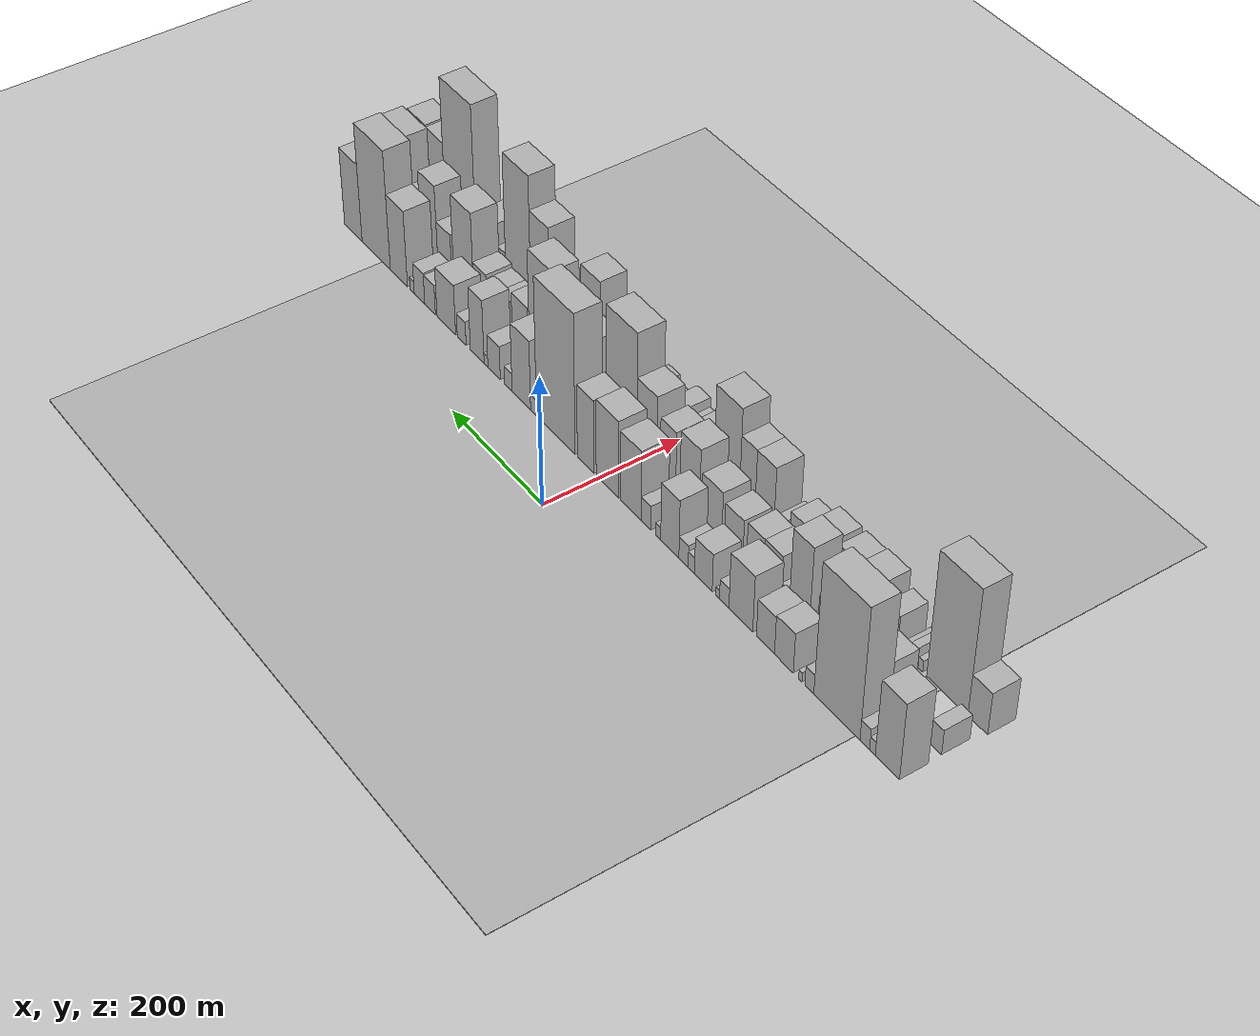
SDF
<?xml version="1.0" encoding="utf-8"?>

<sdf version="1.6">

   <world name="default">

      <gui fullscreen="0">

         <camera name="user_camera">

            <pose>-15 0 4.57585 0 0 0</pose>

            <view_controller>orbit</view_controller>

         </camera>

      </gui>

      <scene>

         <sky>

           <clouds>

             <speed>12</speed>

           </clouds>

         </sky>

         <ambient>0.4 0.4 0.4 1</ambient>

         <background>0.7 0.7 0.7 1</background>

         <shadows>1</shadows>

      </scene>

      <gravity>0 0 -9.8066</gravity>

      <magnetic_field>6e-06 2.3e-05 -4.2e-05</magnetic_field>

      <physics default="0" name="default_physics" type="ode">

         <ode>

            <solver>

               <type>quick</type>

               <iters>10</iters>

               <sor>1.0</sor>

               <use_dynamic_moi_rescaling>0</use_dynamic_moi_rescaling>

            </solver>

            <constraints>

               <cfm>0</cfm>

               <erp>0.2</erp>

               <contact_max_correcting_vel>100</contact_max_correcting_vel>

               <contact_surface_layer>0.001</contact_surface_layer>

            </constraints>

         </ode>

         <max_step_size>0.004</max_step_size>

         <real_time_factor>1</real_time_factor>

         <real_time_update_rate>250</real_time_update_rate>

      </physics>

      <light name="sun" type="directional">

         <cast_shadows>1</cast_shadows>

         <pose>0 0 10 0 0 0</pose>

         <diffuse>0.8 0.8 0.8 1</diffuse>

         <specular>0.2 0.2 0.2 1</specular>

         <attenuation>

            <range>1000</range>

            <constant>0.9</constant>

            <linear>0.01</linear>

            <quadratic>0.001</quadratic>

         </attenuation>

         <direction>-0.5 0.1 -0.9</direction>

      </light>

      <include>

         <name>ground_plane_1</name>

         <uri>model://HANNAS_ground_plane</uri>

         <pose>0 0 0  0 0 0</pose>

      </include>

      <include>

         <name>ground_plane_2</name>

         <uri>model://HANNAS_ground_plane</uri>

         <pose>100 0 0  0 0 0</pose>

      </include>

      <model name="building_1">

         <static>1</static>

         <pose frame="">100.0000 -554.9852 0 0.000000 0.000000 0.000000</pose>

         <link name="link">

            <pose frame="">0 0 60.00 0 0 0</pose>

            <collision name="collision">

               <geometry>

                  <box>

                     <size>40.0000 42.0296 120.0000</size>

                  </box>

               </geometry>

               <max_contacts>10</max_contacts>

               <surface>

                  <contact>

                     <ode/>

                  </contact>

                  <bounce/>

                  <friction>

                     <torsional>

                        <ode/>

                     </torsional>

                     <ode/>

                  </friction>

               </surface>

            </collision>

            <visual name="visual">

               <cast_shadows>0</cast_shadows>

               <geometry>

                  <box>

                     <size>40.0000 42.0296 120.0000</size>

                  </box>

               </geometry>

               <material>

                  <script>

                     <uri>model://HANNAS_wall/materials/scripts</uri>

                     <uri>model://HANNAS_wall/materials/textures</uri>

                     <name>vrc/HANNAS_wall</name>

                  </script>

               </material>

            </visual>

            <self_collide>0</self_collide>

            <enable_wind>0</enable_wind>

            <kinematic>0</kinematic>

         </link>

      </model>

      <model name="building_2">

         <static>1</static>

         <pose frame="">100.0000 -529.0086 0 0.000000 0.000000 0.000000</pose>

         <link name="link">

            <pose frame="">0 0 10.50 0 0 0</pose>

            <collision name="collision">

               <geometry>

                  <box>

                     <size>40.0000 9.9237 21.0000</size>

                  </box>

               </geometry>

               <max_contacts>10</max_contacts>

               <surface>

                  <contact>

                     <ode/>

                  </contact>

                  <bounce/>

                  <friction>

                     <torsional>

                        <ode/>

                     </torsional>

                     <ode/>

                  </friction>

               </surface>

            </collision>

            <visual name="visual">

               <cast_shadows>0</cast_shadows>

               <geometry>

                  <box>

                     <size>40.0000 9.9237 21.0000</size>

                  </box>

               </geometry>

               <material>

                  <script>

                     <uri>model://HANNAS_wall/materials/scripts</uri>

                     <uri>model://HANNAS_wall/materials/textures</uri>

                     <name>vrc/HANNAS_wall</name>

                  </script>

               </material>

            </visual>

            <self_collide>0</self_collide>

            <enable_wind>0</enable_wind>

            <kinematic>0</kinematic>

         </link>

      </model>

      <model name="building_3">

         <static>1</static>

         <pose frame="">100.0000 -515.6214 0 0.000000 0.000000 0.000000</pose>

         <link name="link">

            <pose frame="">0 0 16.50 0 0 0</pose>

            <collision name="collision">

               <geometry>

                  <box>

                     <size>40.0000 16.8506 33.0000</size>

                  </box>

               </geometry>

               <max_contacts>10</max_contacts>

               <surface>

                  <contact>

                     <ode/>

                  </contact>

                  <bounce/>

                  <friction>

                     <torsional>

                        <ode/>

                     </torsional>

                     <ode/>

                  </friction>

               </surface>

            </collision>

            <visual name="visual">

               <cast_shadows>0</cast_shadows>

               <geometry>

                  <box>

                     <size>40.0000 16.8506 33.0000</size>

                  </box>

               </geometry>

               <material>

                  <script>

                     <uri>model://HANNAS_wall/materials/scripts</uri>

                     <uri>model://HANNAS_wall/materials/textures</uri>

                     <name>vrc/HANNAS_wall</name>

                  </script>

               </material>

            </visual>

            <self_collide>0</self_collide>

            <enable_wind>0</enable_wind>

            <kinematic>0</kinematic>

         </link>

      </model>

      <model name="building_4">

         <static>1</static>

         <pose frame="">100.0000 -465.8172 0 0.000000 0.000000 0.000000</pose>

         <link name="link">

            <pose frame="">0 0 103.50 0 0 0</pose>

            <collision name="collision">

               <geometry>

                  <box>

                     <size>40.0000 82.7579 207.0000</size>

                  </box>

               </geometry>

               <max_contacts>10</max_contacts>

               <surface>

                  <contact>

                     <ode/>

                  </contact>

                  <bounce/>

                  <friction>

                     <torsional>

                        <ode/>

                     </torsional>

                     <ode/>

                  </friction>

               </surface>

            </collision>

            <visual name="visual">

               <cast_shadows>0</cast_shadows>

               <geometry>

                  <box>

                     <size>40.0000 82.7579 207.0000</size>

                  </box>

               </geometry>

               <material>

                  <script>

                     <uri>model://HANNAS_wall/materials/scripts</uri>

                     <uri>model://HANNAS_wall/materials/textures</uri>

                     <name>vrc/HANNAS_wall</name>

                  </script>

               </material>

            </visual>

            <self_collide>0</self_collide>

            <enable_wind>0</enable_wind>

            <kinematic>0</kinematic>

         </link>

      </model>

      <model name="building_5">

         <static>1</static>

         <pose frame="">100.0000 -416.1918 0 0.000000 0.000000 0.000000</pose>

         <link name="link">

            <pose frame="">0 0 15.00 0 0 0</pose>

            <collision name="collision">

               <geometry>

                  <box>

                     <size>40.0000 16.4930 30.0000</size>

                  </box>

               </geometry>

               <max_contacts>10</max_contacts>

               <surface>

                  <contact>

                     <ode/>

                  </contact>

                  <bounce/>

                  <friction>

                     <torsional>

                        <ode/>

                     </torsional>

                     <ode/>

                  </friction>

               </surface>

            </collision>

            <visual name="visual">

               <cast_shadows>0</cast_shadows>

               <geometry>

                  <box>

                     <size>40.0000 16.4930 30.0000</size>

                  </box>

               </geometry>

               <material>

                  <script>

                     <uri>model://HANNAS_wall/materials/scripts</uri>

                     <uri>model://HANNAS_wall/materials/textures</uri>

                     <name>vrc/HANNAS_wall</name>

                  </script>

               </material>

            </visual>

            <self_collide>0</self_collide>

            <enable_wind>0</enable_wind>

            <kinematic>0</kinematic>

         </link>

      </model>

      <model name="building_6">

         <static>1</static>

         <pose frame="">100.0000 -399.7806 0 0.000000 0.000000 0.000000</pose>

         <link name="link">

            <pose frame="">0 0 7.50 0 0 0</pose>

            <collision name="collision">

               <geometry>

                  <box>

                     <size>40.0000 6.3295 15.0000</size>

                  </box>

               </geometry>

               <max_contacts>10</max_contacts>

               <surface>

                  <contact>

                     <ode/>

                  </contact>

                  <bounce/>

                  <friction>

                     <torsional>

                        <ode/>

                     </torsional>

                     <ode/>

                  </friction>

               </surface>

            </collision>

            <visual name="visual">

               <cast_shadows>0</cast_shadows>

               <geometry>

                  <box>

                     <size>40.0000 6.3295 15.0000</size>

                  </box>

               </geometry>

               <material>

                  <script>

                     <uri>model://HANNAS_wall/materials/scripts</uri>

                     <uri>model://HANNAS_wall/materials/textures</uri>

                     <name>vrc/HANNAS_wall</name>

                  </script>

               </material>

            </visual>

            <self_collide>0</self_collide>

            <enable_wind>0</enable_wind>

            <kinematic>0</kinematic>

         </link>

      </model>

      <model name="building_7">

         <static>1</static>

         <pose frame="">100.0000 -369.1393 0 0.000000 0.000000 0.000000</pose>

         <link name="link">

            <pose frame="">0 0 31.50 0 0 0</pose>

            <collision name="collision">

               <geometry>

                  <box>

                     <size>40.0000 34.9530 63.0000</size>

                  </box>

               </geometry>

               <max_contacts>10</max_contacts>

               <surface>

                  <contact>

                     <ode/>

                  </contact>

                  <bounce/>

                  <friction>

                     <torsional>

                        <ode/>

                     </torsional>

                     <ode/>

                  </friction>

               </surface>

            </collision>

            <visual name="visual">

               <cast_shadows>0</cast_shadows>

               <geometry>

                  <box>

                     <size>40.0000 34.9530 63.0000</size>

                  </box>

               </geometry>

               <material>

                  <script>

                     <uri>model://HANNAS_wall/materials/scripts</uri>

                     <uri>model://HANNAS_wall/materials/textures</uri>

                     <name>vrc/HANNAS_wall</name>

                  </script>

               </material>

            </visual>

            <self_collide>0</self_collide>

            <enable_wind>0</enable_wind>

            <kinematic>0</kinematic>

         </link>

      </model>

      <model name="building_8">

         <static>1</static>

         <pose frame="">100.0000 -334.6570 0 0.000000 0.000000 0.000000</pose>

         <link name="link">

            <pose frame="">0 0 30.00 0 0 0</pose>

            <collision name="collision">

               <geometry>

                  <box>

                     <size>40.0000 34.0115 60.0000</size>

                  </box>

               </geometry>

               <max_contacts>10</max_contacts>

               <surface>

                  <contact>

                     <ode/>

                  </contact>

                  <bounce/>

                  <friction>

                     <torsional>

                        <ode/>

                     </torsional>

                     <ode/>

                  </friction>

               </surface>

            </collision>

            <visual name="visual">

               <cast_shadows>0</cast_shadows>

               <geometry>

                  <box>

                     <size>40.0000 34.0115 60.0000</size>

                  </box>

               </geometry>

               <material>

                  <script>

                     <uri>model://HANNAS_wall/materials/scripts</uri>

                     <uri>model://HANNAS_wall/materials/textures</uri>

                     <name>vrc/HANNAS_wall</name>

                  </script>

               </material>

            </visual>

            <self_collide>0</self_collide>

            <enable_wind>0</enable_wind>

            <kinematic>0</kinematic>

         </link>

      </model>

      <model name="building_9">

         <static>1</static>

         <pose frame="">100.0000 -287.8549 0 0.000000 0.000000 0.000000</pose>

         <link name="link">

            <pose frame="">0 0 45.00 0 0 0</pose>

            <collision name="collision">

               <geometry>

                  <box>

                     <size>40.0000 45.5928 90.0000</size>

                  </box>

               </geometry>

               <max_contacts>10</max_contacts>

               <surface>

                  <contact>

                     <ode/>

                  </contact>

                  <bounce/>

                  <friction>

                     <torsional>

                        <ode/>

                     </torsional>

                     <ode/>

                  </friction>

               </surface>

            </collision>

            <visual name="visual">

               <cast_shadows>0</cast_shadows>

               <geometry>

                  <box>

                     <size>40.0000 45.5928 90.0000</size>

                  </box>

               </geometry>

               <material>

                  <script>

                     <uri>model://HANNAS_wall/materials/scripts</uri>

                     <uri>model://HANNAS_wall/materials/textures</uri>

                     <name>vrc/HANNAS_wall</name>

                  </script>

               </material>

            </visual>

            <self_collide>0</self_collide>

            <enable_wind>0</enable_wind>

            <kinematic>0</kinematic>

         </link>

      </model>

      <model name="building_10">

         <static>1</static>

         <pose frame="">100.0000 -255.9240 0 0.000000 0.000000 0.000000</pose>

         <link name="link">

            <pose frame="">0 0 16.50 0 0 0</pose>

            <collision name="collision">

               <geometry>

                  <box>

                     <size>40.0000 18.2690 33.0000</size>

                  </box>

               </geometry>

               <max_contacts>10</max_contacts>

               <surface>

                  <contact>

                     <ode/>

                  </contact>

                  <bounce/>

                  <friction>

                     <torsional>

                        <ode/>

                     </torsional>

                     <ode/>

                  </friction>

               </surface>

            </collision>

            <visual name="visual">

               <cast_shadows>0</cast_shadows>

               <geometry>

                  <box>

                     <size>40.0000 18.2690 33.0000</size>

                  </box>

               </geometry>

               <material>

                  <script>

                     <uri>model://HANNAS_wall/materials/scripts</uri>

                     <uri>model://HANNAS_wall/materials/textures</uri>

                     <name>vrc/HANNAS_wall</name>

                  </script>

               </material>

            </visual>

            <self_collide>0</self_collide>

            <enable_wind>0</enable_wind>

            <kinematic>0</kinematic>

         </link>

      </model>

      <model name="building_11">

         <static>1</static>

         <pose frame="">100.0000 -243.1332 0 0.000000 0.000000 0.000000</pose>

         <link name="link">

            <pose frame="">0 0 7.50 0 0 0</pose>

            <collision name="collision">

               <geometry>

                  <box>

                     <size>40.0000 7.3125 15.0000</size>

                  </box>

               </geometry>

               <max_contacts>10</max_contacts>

               <surface>

                  <contact>

                     <ode/>

                  </contact>

                  <bounce/>

                  <friction>

                     <torsional>

                        <ode/>

                     </torsional>

                     <ode/>

                  </friction>

               </surface>

            </collision>

            <visual name="visual">

               <cast_shadows>0</cast_shadows>

               <geometry>

                  <box>

                     <size>40.0000 7.3125 15.0000</size>

                  </box>

               </geometry>

               <material>

                  <script>

                     <uri>model://HANNAS_wall/materials/scripts</uri>

                     <uri>model://HANNAS_wall/materials/textures</uri>

                     <name>vrc/HANNAS_wall</name>

                  </script>

               </material>

            </visual>

            <self_collide>0</self_collide>

            <enable_wind>0</enable_wind>

            <kinematic>0</kinematic>

         </link>

      </model>

      <model name="building_12">

         <static>1</static>

         <pose frame="">100.0000 -215.0559 0 0.000000 0.000000 0.000000</pose>

         <link name="link">

            <pose frame="">0 0 30.00 0 0 0</pose>

            <collision name="collision">

               <geometry>

                  <box>

                     <size>40.0000 34.8422 60.0000</size>

                  </box>

               </geometry>

               <max_contacts>10</max_contacts>

               <surface>

                  <contact>

                     <ode/>

                  </contact>

                  <bounce/>

                  <friction>

                     <torsional>

                        <ode/>

                     </torsional>

                     <ode/>

                  </friction>

               </surface>

            </collision>

            <visual name="visual">

               <cast_shadows>0</cast_shadows>

               <geometry>

                  <box>

                     <size>40.0000 34.8422 60.0000</size>

                  </box>

               </geometry>

               <material>

                  <script>

                     <uri>model://HANNAS_wall/materials/scripts</uri>

                     <uri>model://HANNAS_wall/materials/textures</uri>

                     <name>vrc/HANNAS_wall</name>

                  </script>

               </material>

            </visual>

            <self_collide>0</self_collide>

            <enable_wind>0</enable_wind>

            <kinematic>0</kinematic>

         </link>

      </model>

      <model name="building_13">

         <static>1</static>

         <pose frame="">100.0000 -191.3355 0 0.000000 0.000000 0.000000</pose>

         <link name="link">

            <pose frame="">0 0 13.50 0 0 0</pose>

            <collision name="collision">

               <geometry>

                  <box>

                     <size>40.0000 12.5986 27.0000</size>

                  </box>

               </geometry>

               <max_contacts>10</max_contacts>

               <surface>

                  <contact>

                     <ode/>

                  </contact>

                  <bounce/>

                  <friction>

                     <torsional>

                        <ode/>

                     </torsional>

                     <ode/>

                  </friction>

               </surface>

            </collision>

            <visual name="visual">

               <cast_shadows>0</cast_shadows>

               <geometry>

                  <box>

                     <size>40.0000 12.5986 27.0000</size>

                  </box>

               </geometry>

               <material>

                  <script>

                     <uri>model://HANNAS_wall/materials/scripts</uri>

                     <uri>model://HANNAS_wall/materials/textures</uri>

                     <name>vrc/HANNAS_wall</name>

                  </script>

               </material>

            </visual>

            <self_collide>0</self_collide>

            <enable_wind>0</enable_wind>

            <kinematic>0</kinematic>

         </link>

      </model>

      <model name="building_14">

         <static>1</static>

         <pose frame="">100.0000 -175.7309 0 0.000000 0.000000 0.000000</pose>

         <link name="link">

            <pose frame="">0 0 18.00 0 0 0</pose>

            <collision name="collision">

               <geometry>

                  <box>

                     <size>40.0000 18.6107 36.0000</size>

                  </box>

               </geometry>

               <max_contacts>10</max_contacts>

               <surface>

                  <contact>

                     <ode/>

                  </contact>

                  <bounce/>

                  <friction>

                     <torsional>

                        <ode/>

                     </torsional>

                     <ode/>

                  </friction>

               </surface>

            </collision>

            <visual name="visual">

               <cast_shadows>0</cast_shadows>

               <geometry>

                  <box>

                     <size>40.0000 18.6107 36.0000</size>

                  </box>

               </geometry>

               <material>

                  <script>

                     <uri>model://HANNAS_wall/materials/scripts</uri>

                     <uri>model://HANNAS_wall/materials/textures</uri>

                     <name>vrc/HANNAS_wall</name>

                  </script>

               </material>

            </visual>

            <self_collide>0</self_collide>

            <enable_wind>0</enable_wind>

            <kinematic>0</kinematic>

         </link>

      </model>

      <model name="building_15">

         <static>1</static>

         <pose frame="">100.0000 -148.0607 0 0.000000 0.000000 0.000000</pose>

         <link name="link">

            <pose frame="">0 0 46.50 0 0 0</pose>

            <collision name="collision">

               <geometry>

                  <box>

                     <size>40.0000 36.7295 93.0000</size>

                  </box>

               </geometry>

               <max_contacts>10</max_contacts>

               <surface>

                  <contact>

                     <ode/>

                  </contact>

                  <bounce/>

                  <friction>

                     <torsional>

                        <ode/>

                     </torsional>

                     <ode/>

                  </friction>

               </surface>

            </collision>

            <visual name="visual">

               <cast_shadows>0</cast_shadows>

               <geometry>

                  <box>

                     <size>40.0000 36.7295 93.0000</size>

                  </box>

               </geometry>

               <material>

                  <script>

                     <uri>model://HANNAS_wall/materials/scripts</uri>

                     <uri>model://HANNAS_wall/materials/textures</uri>

                     <name>vrc/HANNAS_wall</name>

                  </script>

               </material>

            </visual>

            <self_collide>0</self_collide>

            <enable_wind>0</enable_wind>

            <kinematic>0</kinematic>

         </link>

      </model>

      <model name="building_16">

         <static>1</static>

         <pose frame="">100.0000 -124.4940 0 0.000000 0.000000 0.000000</pose>

         <link name="link">

            <pose frame="">0 0 10.50 0 0 0</pose>

            <collision name="collision">

               <geometry>

                  <box>

                     <size>40.0000 10.4040 21.0000</size>

                  </box>

               </geometry>

               <max_contacts>10</max_contacts>

               <surface>

                  <contact>

                     <ode/>

                  </contact>

                  <bounce/>

                  <friction>

                     <torsional>

                        <ode/>

                     </torsional>

                     <ode/>

                  </friction>

               </surface>

            </collision>

            <visual name="visual">

               <cast_shadows>0</cast_shadows>

               <geometry>

                  <box>

                     <size>40.0000 10.4040 21.0000</size>

                  </box>

               </geometry>

               <material>

                  <script>

                     <uri>model://HANNAS_wall/materials/scripts</uri>

                     <uri>model://HANNAS_wall/materials/textures</uri>

                     <name>vrc/HANNAS_wall</name>

                  </script>

               </material>

            </visual>

            <self_collide>0</self_collide>

            <enable_wind>0</enable_wind>

            <kinematic>0</kinematic>

         </link>

      </model>

      <model name="building_17">

         <static>1</static>

         <pose frame="">100.0000 -99.4049 0 0.000000 0.000000 0.000000</pose>

         <link name="link">

            <pose frame="">0 0 19.50 0 0 0</pose>

            <collision name="collision">

               <geometry>

                  <box>

                     <size>40.0000 19.7743 39.0000</size>

                  </box>

               </geometry>

               <max_contacts>10</max_contacts>

               <surface>

                  <contact>

                     <ode/>

                  </contact>

                  <bounce/>

                  <friction>

                     <torsional>

                        <ode/>

                     </torsional>

                     <ode/>

                  </friction>

               </surface>

            </collision>

            <visual name="visual">

               <cast_shadows>0</cast_shadows>

               <geometry>

                  <box>

                     <size>40.0000 19.7743 39.0000</size>

                  </box>

               </geometry>

               <material>

                  <script>

                     <uri>model://HANNAS_wall/materials/scripts</uri>

                     <uri>model://HANNAS_wall/materials/textures</uri>

                     <name>vrc/HANNAS_wall</name>

                  </script>

               </material>

            </visual>

            <self_collide>0</self_collide>

            <enable_wind>0</enable_wind>

            <kinematic>0</kinematic>

         </link>

      </model>

      <model name="building_18">

         <static>1</static>

         <pose frame="">100.0000 -67.6563 0 0.000000 0.000000 0.000000</pose>

         <link name="link">

            <pose frame="">0 0 55.50 0 0 0</pose>

            <collision name="collision">

               <geometry>

                  <box>

                     <size>40.0000 43.7229 111.0000</size>

                  </box>

               </geometry>

               <max_contacts>10</max_contacts>

               <surface>

                  <contact>

                     <ode/>

                  </contact>

                  <bounce/>

                  <friction>

                     <torsional>

                        <ode/>

                     </torsional>

                     <ode/>

                  </friction>

               </surface>

            </collision>

            <visual name="visual">

               <cast_shadows>0</cast_shadows>

               <geometry>

                  <box>

                     <size>40.0000 43.7229 111.0000</size>

                  </box>

               </geometry>

               <material>

                  <script>

                     <uri>model://HANNAS_wall/materials/scripts</uri>

                     <uri>model://HANNAS_wall/materials/textures</uri>

                     <name>vrc/HANNAS_wall</name>

                  </script>

               </material>

            </visual>

            <self_collide>0</self_collide>

            <enable_wind>0</enable_wind>

            <kinematic>0</kinematic>

         </link>

      </model>

      <model name="building_19">

         <static>1</static>

         <pose frame="">100.0000 -19.1620 0 0.000000 0.000000 0.000000</pose>

         <link name="link">

            <pose frame="">0 0 61.50 0 0 0</pose>

            <collision name="collision">

               <geometry>

                  <box>

                     <size>40.0000 47.2656 123.0000</size>

                  </box>

               </geometry>

               <max_contacts>10</max_contacts>

               <surface>

                  <contact>

                     <ode/>

                  </contact>

                  <bounce/>

                  <friction>

                     <torsional>

                        <ode/>

                     </torsional>

                     <ode/>

                  </friction>

               </surface>

            </collision>

            <visual name="visual">

               <cast_shadows>0</cast_shadows>

               <geometry>

                  <box>

                     <size>40.0000 47.2656 123.0000</size>

                  </box>

               </geometry>

               <material>

                  <script>

                     <uri>model://HANNAS_wall/materials/scripts</uri>

                     <uri>model://HANNAS_wall/materials/textures</uri>

                     <name>vrc/HANNAS_wall</name>

                  </script>

               </material>

            </visual>

            <self_collide>0</self_collide>

            <enable_wind>0</enable_wind>

            <kinematic>0</kinematic>

         </link>

      </model>

      <model name="building_20">

         <static>1</static>

         <pose frame="">100.0000 27.2043 0 0.000000 0.000000 0.000000</pose>

         <link name="link">

            <pose frame="">0 0 58.50 0 0 0</pose>

            <collision name="collision">

               <geometry>

                  <box>

                     <size>40.0000 35.4669 117.0000</size>

                  </box>

               </geometry>

               <max_contacts>10</max_contacts>

               <surface>

                  <contact>

                     <ode/>

                  </contact>

                  <bounce/>

                  <friction>

                     <torsional>

                        <ode/>

                     </torsional>

                     <ode/>

                  </friction>

               </surface>

            </collision>

            <visual name="visual">

               <cast_shadows>0</cast_shadows>

               <geometry>

                  <box>

                     <size>40.0000 35.4669 117.0000</size>

                  </box>

               </geometry>

               <material>

                  <script>

                     <uri>model://HANNAS_wall/materials/scripts</uri>

                     <uri>model://HANNAS_wall/materials/textures</uri>

                     <name>vrc/HANNAS_wall</name>

                  </script>

               </material>

            </visual>

            <self_collide>0</self_collide>

            <enable_wind>0</enable_wind>

            <kinematic>0</kinematic>

         </link>

      </model>

      <model name="building_21">

         <static>1</static>

         <pose frame="">100.0000 92.3485 0 0.000000 0.000000 0.000000</pose>

         <link name="link">

            <pose frame="">0 0 111.00 0 0 0</pose>

            <collision name="collision">

               <geometry>

                  <box>

                     <size>40.0000 84.8216 222.0000</size>

                  </box>

               </geometry>

               <max_contacts>10</max_contacts>

               <surface>

                  <contact>

                     <ode/>

                  </contact>

                  <bounce/>

                  <friction>

                     <torsional>

                        <ode/>

                     </torsional>

                     <ode/>

                  </friction>

               </surface>

            </collision>

            <visual name="visual">

               <cast_shadows>0</cast_shadows>

               <geometry>

                  <box>

                     <size>40.0000 84.8216 222.0000</size>

                  </box>

               </geometry>

               <material>

                  <script>

                     <uri>model://HANNAS_wall/materials/scripts</uri>

                     <uri>model://HANNAS_wall/materials/textures</uri>

                     <name>vrc/HANNAS_wall</name>

                  </script>

               </material>

            </visual>

            <self_collide>0</self_collide>

            <enable_wind>0</enable_wind>

            <kinematic>0</kinematic>

         </link>

      </model>

      <model name="building_22">

         <static>1</static>

         <pose frame="">100.0000 141.3330 0 0.000000 0.000000 0.000000</pose>

         <link name="link">

            <pose frame="">0 0 13.50 0 0 0</pose>

            <collision name="collision">

               <geometry>

                  <box>

                     <size>40.0000 13.1473 27.0000</size>

                  </box>

               </geometry>

               <max_contacts>10</max_contacts>

               <surface>

                  <contact>

                     <ode/>

                  </contact>

                  <bounce/>

                  <friction>

                     <torsional>

                        <ode/>

                     </torsional>

                     <ode/>

                  </friction>

               </surface>

            </collision>

            <visual name="visual">

               <cast_shadows>0</cast_shadows>

               <geometry>

                  <box>

                     <size>40.0000 13.1473 27.0000</size>

                  </box>

               </geometry>

               <material>

                  <script>

                     <uri>model://HANNAS_wall/materials/scripts</uri>

                     <uri>model://HANNAS_wall/materials/textures</uri>

                     <name>vrc/HANNAS_wall</name>

                  </script>

               </material>

            </visual>

            <self_collide>0</self_collide>

            <enable_wind>0</enable_wind>

            <kinematic>0</kinematic>

         </link>

      </model>

      <model name="building_23">

         <static>1</static>

         <pose frame="">100.0000 168.8270 0 0.000000 0.000000 0.000000</pose>

         <link name="link">

            <pose frame="">0 0 55.50 0 0 0</pose>

            <collision name="collision">

               <geometry>

                  <box>

                     <size>40.0000 41.8408 111.0000</size>

                  </box>

               </geometry>

               <max_contacts>10</max_contacts>

               <surface>

                  <contact>

                     <ode/>

                  </contact>

                  <bounce/>

                  <friction>

                     <torsional>

                        <ode/>

                     </torsional>

                     <ode/>

                  </friction>

               </surface>

            </collision>

            <visual name="visual">

               <cast_shadows>0</cast_shadows>

               <geometry>

                  <box>

                     <size>40.0000 41.8408 111.0000</size>

                  </box>

               </geometry>

               <material>

                  <script>

                     <uri>model://HANNAS_wall/materials/scripts</uri>

                     <uri>model://HANNAS_wall/materials/textures</uri>

                     <name>vrc/HANNAS_wall</name>

                  </script>

               </material>

            </visual>

            <self_collide>0</self_collide>

            <enable_wind>0</enable_wind>

            <kinematic>0</kinematic>

         </link>

      </model>

      <model name="building_24">

         <static>1</static>

         <pose frame="">100.0000 198.2511 0 0.000000 0.000000 0.000000</pose>

         <link name="link">

            <pose frame="">0 0 15.00 0 0 0</pose>

            <collision name="collision">

               <geometry>

                  <box>

                     <size>40.0000 17.0074 30.0000</size>

                  </box>

               </geometry>

               <max_contacts>10</max_contacts>

               <surface>

                  <contact>

                     <ode/>

                  </contact>

                  <bounce/>

                  <friction>

                     <torsional>

                        <ode/>

                     </torsional>

                     <ode/>

                  </friction>

               </surface>

            </collision>

            <visual name="visual">

               <cast_shadows>0</cast_shadows>

               <geometry>

                  <box>

                     <size>40.0000 17.0074 30.0000</size>

                  </box>

               </geometry>

               <material>

                  <script>

                     <uri>model://HANNAS_wall/materials/scripts</uri>

                     <uri>model://HANNAS_wall/materials/textures</uri>

                     <name>vrc/HANNAS_wall</name>

                  </script>

               </material>

            </visual>

            <self_collide>0</self_collide>

            <enable_wind>0</enable_wind>

            <kinematic>0</kinematic>

         </link>

      </model>

      <model name="building_25">

         <static>1</static>

         <pose frame="">100.0000 231.0359 0 0.000000 0.000000 0.000000</pose>

         <link name="link">

            <pose frame="">0 0 27.00 0 0 0</pose>

            <collision name="collision">

               <geometry>

                  <box>

                     <size>40.0000 28.5621 54.0000</size>

                  </box>

               </geometry>

               <max_contacts>10</max_contacts>

               <surface>

                  <contact>

                     <ode/>

                  </contact>

                  <bounce/>

                  <friction>

                     <torsional>

                        <ode/>

                     </torsional>

                     <ode/>

                  </friction>

               </surface>

            </collision>

            <visual name="visual">

               <cast_shadows>0</cast_shadows>

               <geometry>

                  <box>

                     <size>40.0000 28.5621 54.0000</size>

                  </box>

               </geometry>

               <material>

                  <script>

                     <uri>model://HANNAS_wall/materials/scripts</uri>

                     <uri>model://HANNAS_wall/materials/textures</uri>

                     <name>vrc/HANNAS_wall</name>

                  </script>

               </material>

            </visual>

            <self_collide>0</self_collide>

            <enable_wind>0</enable_wind>

            <kinematic>0</kinematic>

         </link>

      </model>

      <model name="building_26">

         <static>1</static>

         <pose frame="">100.0000 249.7770 0 0.000000 0.000000 0.000000</pose>

         <link name="link">

            <pose frame="">0 0 9.00 0 0 0</pose>

            <collision name="collision">

               <geometry>

                  <box>

                     <size>40.0000 8.9201 18.0000</size>

                  </box>

               </geometry>

               <max_contacts>10</max_contacts>

               <surface>

                  <contact>

                     <ode/>

                  </contact>

                  <bounce/>

                  <friction>

                     <torsional>

                        <ode/>

                     </torsional>

                     <ode/>

                  </friction>

               </surface>

            </collision>

            <visual name="visual">

               <cast_shadows>0</cast_shadows>

               <geometry>

                  <box>

                     <size>40.0000 8.9201 18.0000</size>

                  </box>

               </geometry>

               <material>

                  <script>

                     <uri>model://HANNAS_wall/materials/scripts</uri>

                     <uri>model://HANNAS_wall/materials/textures</uri>

                     <name>vrc/HANNAS_wall</name>

                  </script>

               </material>

            </visual>

            <self_collide>0</self_collide>

            <enable_wind>0</enable_wind>

            <kinematic>0</kinematic>

         </link>

      </model>

      <model name="building_27">

         <static>1</static>

         <pose frame="">100.0000 270.2327 0 0.000000 0.000000 0.000000</pose>

         <link name="link">

            <pose frame="">0 0 51.00 0 0 0</pose>

            <collision name="collision">

               <geometry>

                  <box>

                     <size>40.0000 31.9914 102.0000</size>

                  </box>

               </geometry>

               <max_contacts>10</max_contacts>

               <surface>

                  <contact>

                     <ode/>

                  </contact>

                  <bounce/>

                  <friction>

                     <torsional>

                        <ode/>

                     </torsional>

                     <ode/>

                  </friction>

               </surface>

            </collision>

            <visual name="visual">

               <cast_shadows>0</cast_shadows>

               <geometry>

                  <box>

                     <size>40.0000 31.9914 102.0000</size>

                  </box>

               </geometry>

               <material>

                  <script>

                     <uri>model://HANNAS_wall/materials/scripts</uri>

                     <uri>model://HANNAS_wall/materials/textures</uri>

                     <name>vrc/HANNAS_wall</name>

                  </script>

               </material>

            </visual>

            <self_collide>0</self_collide>

            <enable_wind>0</enable_wind>

            <kinematic>0</kinematic>

         </link>

      </model>

      <model name="building_28">

         <static>1</static>

         <pose frame="">100.0000 306.6255 0 0.000000 0.000000 0.000000</pose>

         <link name="link">

            <pose frame="">0 0 19.50 0 0 0</pose>

            <collision name="collision">

               <geometry>

                  <box>

                     <size>40.0000 20.7942 39.0000</size>

                  </box>

               </geometry>

               <max_contacts>10</max_contacts>

               <surface>

                  <contact>

                     <ode/>

                  </contact>

                  <bounce/>

                  <friction>

                     <torsional>

                        <ode/>

                     </torsional>

                     <ode/>

                  </friction>

               </surface>

            </collision>

            <visual name="visual">

               <cast_shadows>0</cast_shadows>

               <geometry>

                  <box>

                     <size>40.0000 20.7942 39.0000</size>

                  </box>

               </geometry>

               <material>

                  <script>

                     <uri>model://HANNAS_wall/materials/scripts</uri>

                     <uri>model://HANNAS_wall/materials/textures</uri>

                     <name>vrc/HANNAS_wall</name>

                  </script>

               </material>

            </visual>

            <self_collide>0</self_collide>

            <enable_wind>0</enable_wind>

            <kinematic>0</kinematic>

         </link>

      </model>

      <model name="building_29">

         <static>1</static>

         <pose frame="">100.0000 343.2490 0 0.000000 0.000000 0.000000</pose>

         <link name="link">

            <pose frame="">0 0 40.50 0 0 0</pose>

            <collision name="collision">

               <geometry>

                  <box>

                     <size>40.0000 44.4526 81.0000</size>

                  </box>

               </geometry>

               <max_contacts>10</max_contacts>

               <surface>

                  <contact>

                     <ode/>

                  </contact>

                  <bounce/>

                  <friction>

                     <torsional>

                        <ode/>

                     </torsional>

                     <ode/>

                  </friction>

               </surface>

            </collision>

            <visual name="visual">

               <cast_shadows>0</cast_shadows>

               <geometry>

                  <box>

                     <size>40.0000 44.4526 81.0000</size>

                  </box>

               </geometry>

               <material>

                  <script>

                     <uri>model://HANNAS_wall/materials/scripts</uri>

                     <uri>model://HANNAS_wall/materials/textures</uri>

                     <name>vrc/HANNAS_wall</name>

                  </script>

               </material>

            </visual>

            <self_collide>0</self_collide>

            <enable_wind>0</enable_wind>

            <kinematic>0</kinematic>

         </link>

      </model>

      <model name="building_30">

         <static>1</static>

         <pose frame="">100.0000 382.4299 0 0.000000 0.000000 0.000000</pose>

         <link name="link">

            <pose frame="">0 0 24.00 0 0 0</pose>

            <collision name="collision">

               <geometry>

                  <box>

                     <size>40.0000 25.9092 48.0000</size>

                  </box>

               </geometry>

               <max_contacts>10</max_contacts>

               <surface>

                  <contact>

                     <ode/>

                  </contact>

                  <bounce/>

                  <friction>

                     <torsional>

                        <ode/>

                     </torsional>

                     <ode/>

                  </friction>

               </surface>

            </collision>

            <visual name="visual">

               <cast_shadows>0</cast_shadows>

               <geometry>

                  <box>

                     <size>40.0000 25.9092 48.0000</size>

                  </box>

               </geometry>

               <material>

                  <script>

                     <uri>model://HANNAS_wall/materials/scripts</uri>

                     <uri>model://HANNAS_wall/materials/textures</uri>

                     <name>vrc/HANNAS_wall</name>

                  </script>

               </material>

            </visual>

            <self_collide>0</self_collide>

            <enable_wind>0</enable_wind>

            <kinematic>0</kinematic>

         </link>

      </model>

      <model name="building_31">

         <static>1</static>

         <pose frame="">100.0000 408.2761 0 0.000000 0.000000 0.000000</pose>

         <link name="link">

            <pose frame="">0 0 25.50 0 0 0</pose>

            <collision name="collision">

               <geometry>

                  <box>

                     <size>40.0000 25.7833 51.0000</size>

                  </box>

               </geometry>

               <max_contacts>10</max_contacts>

               <surface>

                  <contact>

                     <ode/>

                  </contact>

                  <bounce/>

                  <friction>

                     <torsional>

                        <ode/>

                     </torsional>

                     <ode/>

                  </friction>

               </surface>

            </collision>

            <visual name="visual">

               <cast_shadows>0</cast_shadows>

               <geometry>

                  <box>

                     <size>40.0000 25.7833 51.0000</size>

                  </box>

               </geometry>

               <material>

                  <script>

                     <uri>model://HANNAS_wall/materials/scripts</uri>

                     <uri>model://HANNAS_wall/materials/textures</uri>

                     <name>vrc/HANNAS_wall</name>

                  </script>

               </material>

            </visual>

            <self_collide>0</self_collide>

            <enable_wind>0</enable_wind>

            <kinematic>0</kinematic>

         </link>

      </model>

      <model name="building_32">

         <static>1</static>

         <pose frame="">100.0000 426.4053 0 0.000000 0.000000 0.000000</pose>

         <link name="link">

            <pose frame="">0 0 10.50 0 0 0</pose>

            <collision name="collision">

               <geometry>

                  <box>

                     <size>40.0000 10.4751 21.0000</size>

                  </box>

               </geometry>

               <max_contacts>10</max_contacts>

               <surface>

                  <contact>

                     <ode/>

                  </contact>

                  <bounce/>

                  <friction>

                     <torsional>

                        <ode/>

                     </torsional>

                     <ode/>

                  </friction>

               </surface>

            </collision>

            <visual name="visual">

               <cast_shadows>0</cast_shadows>

               <geometry>

                  <box>

                     <size>40.0000 10.4751 21.0000</size>

                  </box>

               </geometry>

               <material>

                  <script>

                     <uri>model://HANNAS_wall/materials/scripts</uri>

                     <uri>model://HANNAS_wall/materials/textures</uri>

                     <name>vrc/HANNAS_wall</name>

                  </script>

               </material>

            </visual>

            <self_collide>0</self_collide>

            <enable_wind>0</enable_wind>

            <kinematic>0</kinematic>

         </link>

      </model>

      <model name="building_33">

         <static>1</static>

         <pose frame="">100.0000 459.0152 0 0.000000 0.000000 0.000000</pose>

         <link name="link">

            <pose frame="">0 0 61.50 0 0 0</pose>

            <collision name="collision">

               <geometry>

                  <box>

                     <size>40.0000 42.7447 123.0000</size>

                  </box>

               </geometry>

               <max_contacts>10</max_contacts>

               <surface>

                  <contact>

                     <ode/>

                  </contact>

                  <bounce/>

                  <friction>

                     <torsional>

                        <ode/>

                     </torsional>

                     <ode/>

                  </friction>

               </surface>

            </collision>

            <visual name="visual">

               <cast_shadows>0</cast_shadows>

               <geometry>

                  <box>

                     <size>40.0000 42.7447 123.0000</size>

                  </box>

               </geometry>

               <material>

                  <script>

                     <uri>model://HANNAS_wall/materials/scripts</uri>

                     <uri>model://HANNAS_wall/materials/textures</uri>

                     <name>vrc/HANNAS_wall</name>

                  </script>

               </material>

            </visual>

            <self_collide>0</self_collide>

            <enable_wind>0</enable_wind>

            <kinematic>0</kinematic>

         </link>

      </model>

      <model name="building_34">

         <static>1</static>

         <pose frame="">100.0000 516.2452 0 0.000000 0.000000 0.000000</pose>

         <link name="link">

            <pose frame="">0 0 96.00 0 0 0</pose>

            <collision name="collision">

               <geometry>

                  <box>

                     <size>40.0000 71.7153 192.0000</size>

                  </box>

               </geometry>

               <max_contacts>10</max_contacts>

               <surface>

                  <contact>

                     <ode/>

                  </contact>

                  <bounce/>

                  <friction>

                     <torsional>

                        <ode/>

                     </torsional>

                     <ode/>

                  </friction>

               </surface>

            </collision>

            <visual name="visual">

               <cast_shadows>0</cast_shadows>

               <geometry>

                  <box>

                     <size>40.0000 71.7153 192.0000</size>

                  </box>

               </geometry>

               <material>

                  <script>

                     <uri>model://HANNAS_wall/materials/scripts</uri>

                     <uri>model://HANNAS_wall/materials/textures</uri>

                     <name>vrc/HANNAS_wall</name>

                  </script>

               </material>

            </visual>

            <self_collide>0</self_collide>

            <enable_wind>0</enable_wind>

            <kinematic>0</kinematic>

         </link>

      </model>

      <model name="building_35">

         <static>1</static>

         <pose frame="">100.0000 574.6132 0 0.000000 0.000000 0.000000</pose>

         <link name="link">

            <pose frame="">0 0 63.00 0 0 0</pose>

            <collision name="collision">

               <geometry>

                  <box>

                     <size>40.0000 45.0207 126.0000</size>

                  </box>

               </geometry>

               <max_contacts>10</max_contacts>

               <surface>

                  <contact>

                     <ode/>

                  </contact>

                  <bounce/>

                  <friction>

                     <torsional>

                        <ode/>

                     </torsional>

                     <ode/>

                  </friction>

               </surface>

            </collision>

            <visual name="visual">

               <cast_shadows>0</cast_shadows>

               <geometry>

                  <box>

                     <size>40.0000 45.0207 126.0000</size>

                  </box>

               </geometry>

               <material>

                  <script>

                     <uri>model://HANNAS_wall/materials/scripts</uri>

                     <uri>model://HANNAS_wall/materials/textures</uri>

                     <name>vrc/HANNAS_wall</name>

                  </script>

               </material>

            </visual>

            <self_collide>0</self_collide>

            <enable_wind>0</enable_wind>

            <kinematic>0</kinematic>

         </link>

      </model>

      <model name="building_36">

         <static>1</static>

         <pose frame="">160.0000 -564.1067 0 0.000000 0.000000 0.000000</pose>

         <link name="link">

            <pose frame="">0 0 19.50 0 0 0</pose>

            <collision name="collision">

               <geometry>

                  <box>

                     <size>40.0000 19.7865 39.0000</size>

                  </box>

               </geometry>

               <max_contacts>10</max_contacts>

               <surface>

                  <contact>

                     <ode/>

                  </contact>

                  <bounce/>

                  <friction>

                     <torsional>

                        <ode/>

                     </torsional>

                     <ode/>

                  </friction>

               </surface>

            </collision>

            <visual name="visual">

               <cast_shadows>0</cast_shadows>

               <geometry>

                  <box>

                     <size>40.0000 19.7865 39.0000</size>

                  </box>

               </geometry>

               <material>

                  <script>

                     <uri>model://HANNAS_wall/materials/scripts</uri>

                     <uri>model://HANNAS_wall/materials/textures</uri>

                     <name>vrc/HANNAS_wall</name>

                  </script>

               </material>

            </visual>

            <self_collide>0</self_collide>

            <enable_wind>0</enable_wind>

            <kinematic>0</kinematic>

         </link>

      </model>

      <model name="building_37">

         <static>1</static>

         <pose frame="">160.0000 -462.3433 0 0.000000 0.000000 0.000000</pose>

         <link name="link">

            <pose frame="">0 0 30.00 0 0 0</pose>

            <collision name="collision">

               <geometry>

                  <box>

                     <size>40.0000 34.5801 60.0000</size>

                  </box>

               </geometry>

               <max_contacts>10</max_contacts>

               <surface>

                  <contact>

                     <ode/>

                  </contact>

                  <bounce/>

                  <friction>

                     <torsional>

                        <ode/>

                     </torsional>

                     <ode/>

                  </friction>

               </surface>

            </collision>

            <visual name="visual">

               <cast_shadows>0</cast_shadows>

               <geometry>

                  <box>

                     <size>40.0000 34.5801 60.0000</size>

                  </box>

               </geometry>

               <material>

                  <script>

                     <uri>model://HANNAS_wall/materials/scripts</uri>

                     <uri>model://HANNAS_wall/materials/textures</uri>

                     <name>vrc/HANNAS_wall</name>

                  </script>

               </material>

            </visual>

            <self_collide>0</self_collide>

            <enable_wind>0</enable_wind>

            <kinematic>0</kinematic>

         </link>

      </model>

      <model name="building_38">

         <static>1</static>

         <pose frame="">160.0000 -436.7394 0 0.000000 0.000000 0.000000</pose>

         <link name="link">

            <pose frame="">0 0 16.50 0 0 0</pose>

            <collision name="collision">

               <geometry>

                  <box>

                     <size>40.0000 16.6276 33.0000</size>

                  </box>

               </geometry>

               <max_contacts>10</max_contacts>

               <surface>

                  <contact>

                     <ode/>

                  </contact>

                  <bounce/>

                  <friction>

                     <torsional>

                        <ode/>

                     </torsional>

                     <ode/>

                  </friction>

               </surface>

            </collision>

            <visual name="visual">

               <cast_shadows>0</cast_shadows>

               <geometry>

                  <box>

                     <size>40.0000 16.6276 33.0000</size>

                  </box>

               </geometry>

               <material>

                  <script>

                     <uri>model://HANNAS_wall/materials/scripts</uri>

                     <uri>model://HANNAS_wall/materials/textures</uri>

                     <name>vrc/HANNAS_wall</name>

                  </script>

               </material>

            </visual>

            <self_collide>0</self_collide>

            <enable_wind>0</enable_wind>

            <kinematic>0</kinematic>

         </link>

      </model>

      <model name="building_39">

         <static>1</static>

         <pose frame="">160.0000 -405.9853 0 0.000000 0.000000 0.000000</pose>

         <link name="link">

            <pose frame="">0 0 39.00 0 0 0</pose>

            <collision name="collision">

               <geometry>

                  <box>

                     <size>40.0000 44.8807 78.0000</size>

                  </box>

               </geometry>

               <max_contacts>10</max_contacts>

               <surface>

                  <contact>

                     <ode/>

                  </contact>

                  <bounce/>

                  <friction>

                     <torsional>

                        <ode/>

                     </torsional>

                     <ode/>

                  </friction>

               </surface>

            </collision>

            <visual name="visual">

               <cast_shadows>0</cast_shadows>

               <geometry>

                  <box>

                     <size>40.0000 44.8807 78.0000</size>

                  </box>

               </geometry>

               <material>

                  <script>

                     <uri>model://HANNAS_wall/materials/scripts</uri>

                     <uri>model://HANNAS_wall/materials/textures</uri>

                     <name>vrc/HANNAS_wall</name>

                  </script>

               </material>

            </visual>

            <self_collide>0</self_collide>

            <enable_wind>0</enable_wind>

            <kinematic>0</kinematic>

         </link>

      </model>

      <model name="building_40">

         <static>1</static>

         <pose frame="">160.0000 -367.8634 0 0.000000 0.000000 0.000000</pose>

         <link name="link">

            <pose frame="">0 0 30.00 0 0 0</pose>

            <collision name="collision">

               <geometry>

                  <box>

                     <size>40.0000 31.3629 60.0000</size>

                  </box>

               </geometry>

               <max_contacts>10</max_contacts>

               <surface>

                  <contact>

                     <ode/>

                  </contact>

                  <bounce/>

                  <friction>

                     <torsional>

                        <ode/>

                     </torsional>

                     <ode/>

                  </friction>

               </surface>

            </collision>

            <visual name="visual">

               <cast_shadows>0</cast_shadows>

               <geometry>

                  <box>

                     <size>40.0000 31.3629 60.0000</size>

                  </box>

               </geometry>

               <material>

                  <script>

                     <uri>model://HANNAS_wall/materials/scripts</uri>

                     <uri>model://HANNAS_wall/materials/textures</uri>

                     <name>vrc/HANNAS_wall</name>

                  </script>

               </material>

            </visual>

            <self_collide>0</self_collide>

            <enable_wind>0</enable_wind>

            <kinematic>0</kinematic>

         </link>

      </model>

      <model name="building_41">

         <static>1</static>

         <pose frame="">160.0000 -349.0872 0 0.000000 0.000000 0.000000</pose>

         <link name="link">

            <pose frame="">0 0 7.50 0 0 0</pose>

            <collision name="collision">

               <geometry>

                  <box>

                     <size>40.0000 6.1896 15.0000</size>

                  </box>

               </geometry>

               <max_contacts>10</max_contacts>

               <surface>

                  <contact>

                     <ode/>

                  </contact>

                  <bounce/>

                  <friction>

                     <torsional>

                        <ode/>

                     </torsional>

                     <ode/>

                  </friction>

               </surface>

            </collision>

            <visual name="visual">

               <cast_shadows>0</cast_shadows>

               <geometry>

                  <box>

                     <size>40.0000 6.1896 15.0000</size>

                  </box>

               </geometry>

               <material>

                  <script>

                     <uri>model://HANNAS_wall/materials/scripts</uri>

                     <uri>model://HANNAS_wall/materials/textures</uri>

                     <name>vrc/HANNAS_wall</name>

                  </script>

               </material>

            </visual>

            <self_collide>0</self_collide>

            <enable_wind>0</enable_wind>

            <kinematic>0</kinematic>

         </link>

      </model>

      <model name="building_42">

         <static>1</static>

         <pose frame="">160.0000 -341.9217 0 0.000000 0.000000 0.000000</pose>

         <link name="link">

            <pose frame="">0 0 9.00 0 0 0</pose>

            <collision name="collision">

               <geometry>

                  <box>

                     <size>40.0000 8.1414 18.0000</size>

                  </box>

               </geometry>

               <max_contacts>10</max_contacts>

               <surface>

                  <contact>

                     <ode/>

                  </contact>

                  <bounce/>

                  <friction>

                     <torsional>

                        <ode/>

                     </torsional>

                     <ode/>

                  </friction>

               </surface>

            </collision>

            <visual name="visual">

               <cast_shadows>0</cast_shadows>

               <geometry>

                  <box>

                     <size>40.0000 8.1414 18.0000</size>

                  </box>

               </geometry>

               <material>

                  <script>

                     <uri>model://HANNAS_wall/materials/scripts</uri>

                     <uri>model://HANNAS_wall/materials/textures</uri>

                     <name>vrc/HANNAS_wall</name>

                  </script>

               </material>

            </visual>

            <self_collide>0</self_collide>

            <enable_wind>0</enable_wind>

            <kinematic>0</kinematic>

         </link>

      </model>

      <model name="building_43">

         <static>1</static>

         <pose frame="">160.0000 -318.8556 0 0.000000 0.000000 0.000000</pose>

         <link name="link">

            <pose frame="">0 0 61.50 0 0 0</pose>

            <collision name="collision">

               <geometry>

                  <box>

                     <size>40.0000 37.9908 123.0000</size>

                  </box>

               </geometry>

               <max_contacts>10</max_contacts>

               <surface>

                  <contact>

                     <ode/>

                  </contact>

                  <bounce/>

                  <friction>

                     <torsional>

                        <ode/>

                     </torsional>

                     <ode/>

                  </friction>

               </surface>

            </collision>

            <visual name="visual">

               <cast_shadows>0</cast_shadows>

               <geometry>

                  <box>

                     <size>40.0000 37.9908 123.0000</size>

                  </box>

               </geometry>

               <material>

                  <script>

                     <uri>model://HANNAS_wall/materials/scripts</uri>

                     <uri>model://HANNAS_wall/materials/textures</uri>

                     <name>vrc/HANNAS_wall</name>

                  </script>

               </material>

            </visual>

            <self_collide>0</self_collide>

            <enable_wind>0</enable_wind>

            <kinematic>0</kinematic>

         </link>

      </model>

      <model name="building_44">

         <static>1</static>

         <pose frame="">160.0000 -290.0937 0 0.000000 0.000000 0.000000</pose>

         <link name="link">

            <pose frame="">0 0 12.00 0 0 0</pose>

            <collision name="collision">

               <geometry>

                  <box>

                     <size>40.0000 11.5330 24.0000</size>

                  </box>

               </geometry>

               <max_contacts>10</max_contacts>

               <surface>

                  <contact>

                     <ode/>

                  </contact>

                  <bounce/>

                  <friction>

                     <torsional>

                        <ode/>

                     </torsional>

                     <ode/>

                  </friction>

               </surface>

            </collision>

            <visual name="visual">

               <cast_shadows>0</cast_shadows>

               <geometry>

                  <box>

                     <size>40.0000 11.5330 24.0000</size>

                  </box>

               </geometry>

               <material>

                  <script>

                     <uri>model://HANNAS_wall/materials/scripts</uri>

                     <uri>model://HANNAS_wall/materials/textures</uri>

                     <name>vrc/HANNAS_wall</name>

                  </script>

               </material>

            </visual>

            <self_collide>0</self_collide>

            <enable_wind>0</enable_wind>

            <kinematic>0</kinematic>

         </link>

      </model>

      <model name="building_45">

         <static>1</static>

         <pose frame="">160.0000 -267.5681 0 0.000000 0.000000 0.000000</pose>

         <link name="link">

            <pose frame="">0 0 33.00 0 0 0</pose>

            <collision name="collision">

               <geometry>

                  <box>

                     <size>40.0000 33.5183 66.0000</size>

                  </box>

               </geometry>

               <max_contacts>10</max_contacts>

               <surface>

                  <contact>

                     <ode/>

                  </contact>

                  <bounce/>

                  <friction>

                     <torsional>

                        <ode/>

                     </torsional>

                     <ode/>

                  </friction>

               </surface>

            </collision>

            <visual name="visual">

               <cast_shadows>0</cast_shadows>

               <geometry>

                  <box>

                     <size>40.0000 33.5183 66.0000</size>

                  </box>

               </geometry>

               <material>

                  <script>

                     <uri>model://HANNAS_wall/materials/scripts</uri>

                     <uri>model://HANNAS_wall/materials/textures</uri>

                     <name>vrc/HANNAS_wall</name>

                  </script>

               </material>

            </visual>

            <self_collide>0</self_collide>

            <enable_wind>0</enable_wind>

            <kinematic>0</kinematic>

         </link>

      </model>

      <model name="building_46">

         <static>1</static>

         <pose frame="">160.0000 -234.0867 0 0.000000 0.000000 0.000000</pose>

         <link name="link">

            <pose frame="">0 0 33.00 0 0 0</pose>

            <collision name="collision">

               <geometry>

                  <box>

                     <size>40.0000 33.4445 66.0000</size>

                  </box>

               </geometry>

               <max_contacts>10</max_contacts>

               <surface>

                  <contact>

                     <ode/>

                  </contact>

                  <bounce/>

                  <friction>

                     <torsional>

                        <ode/>

                     </torsional>

                     <ode/>

                  </friction>

               </surface>

            </collision>

            <visual name="visual">

               <cast_shadows>0</cast_shadows>

               <geometry>

                  <box>

                     <size>40.0000 33.4445 66.0000</size>

                  </box>

               </geometry>

               <material>

                  <script>

                     <uri>model://HANNAS_wall/materials/scripts</uri>

                     <uri>model://HANNAS_wall/materials/textures</uri>

                     <name>vrc/HANNAS_wall</name>

                  </script>

               </material>

            </visual>

            <self_collide>0</self_collide>

            <enable_wind>0</enable_wind>

            <kinematic>0</kinematic>

         </link>

      </model>

      <model name="building_47">

         <static>1</static>

         <pose frame="">160.0000 -192.1216 0 0.000000 0.000000 0.000000</pose>

         <link name="link">

            <pose frame="">0 0 31.50 0 0 0</pose>

            <collision name="collision">

               <geometry>

                  <box>

                     <size>40.0000 36.4857 63.0000</size>

                  </box>

               </geometry>

               <max_contacts>10</max_contacts>

               <surface>

                  <contact>

                     <ode/>

                  </contact>

                  <bounce/>

                  <friction>

                     <torsional>

                        <ode/>

                     </torsional>

                     <ode/>

                  </friction>

               </surface>

            </collision>

            <visual name="visual">

               <cast_shadows>0</cast_shadows>

               <geometry>

                  <box>

                     <size>40.0000 36.4857 63.0000</size>

                  </box>

               </geometry>

               <material>

                  <script>

                     <uri>model://HANNAS_wall/materials/scripts</uri>

                     <uri>model://HANNAS_wall/materials/textures</uri>

                     <name>vrc/HANNAS_wall</name>

                  </script>

               </material>

            </visual>

            <self_collide>0</self_collide>

            <enable_wind>0</enable_wind>

            <kinematic>0</kinematic>

         </link>

      </model>

      <model name="building_48">

         <static>1</static>

         <pose frame="">160.0000 -148.4289 0 0.000000 0.000000 0.000000</pose>

         <link name="link">

            <pose frame="">0 0 37.50 0 0 0</pose>

            <collision name="collision">

               <geometry>

                  <box>

                     <size>40.0000 40.8998 75.0000</size>

                  </box>

               </geometry>

               <max_contacts>10</max_contacts>

               <surface>

                  <contact>

                     <ode/>

                  </contact>

                  <bounce/>

                  <friction>

                     <torsional>

                        <ode/>

                     </torsional>

                     <ode/>

                  </friction>

               </surface>

            </collision>

            <visual name="visual">

               <cast_shadows>0</cast_shadows>

               <geometry>

                  <box>

                     <size>40.0000 40.8998 75.0000</size>

                  </box>

               </geometry>

               <material>

                  <script>

                     <uri>model://HANNAS_wall/materials/scripts</uri>

                     <uri>model://HANNAS_wall/materials/textures</uri>

                     <name>vrc/HANNAS_wall</name>

                  </script>

               </material>

            </visual>

            <self_collide>0</self_collide>

            <enable_wind>0</enable_wind>

            <kinematic>0</kinematic>

         </link>

      </model>

      <model name="building_49">

         <static>1</static>

         <pose frame="">160.0000 -104.0006 0 0.000000 0.000000 0.000000</pose>

         <link name="link">

            <pose frame="">0 0 54.00 0 0 0</pose>

            <collision name="collision">

               <geometry>

                  <box>

                     <size>40.0000 39.9567 108.0000</size>

                  </box>

               </geometry>

               <max_contacts>10</max_contacts>

               <surface>

                  <contact>

                     <ode/>

                  </contact>

                  <bounce/>

                  <friction>

                     <torsional>

                        <ode/>

                     </torsional>

                     <ode/>

                  </friction>

               </surface>

            </collision>

            <visual name="visual">

               <cast_shadows>0</cast_shadows>

               <geometry>

                  <box>

                     <size>40.0000 39.9567 108.0000</size>

                  </box>

               </geometry>

               <material>

                  <script>

                     <uri>model://HANNAS_wall/materials/scripts</uri>

                     <uri>model://HANNAS_wall/materials/textures</uri>

                     <name>vrc/HANNAS_wall</name>

                  </script>

               </material>

            </visual>

            <self_collide>0</self_collide>

            <enable_wind>0</enable_wind>

            <kinematic>0</kinematic>

         </link>

      </model>

      <model name="building_50">

         <static>1</static>

         <pose frame="">160.0000 -79.7294 0 0.000000 0.000000 0.000000</pose>

         <link name="link">

            <pose frame="">0 0 9.00 0 0 0</pose>

            <collision name="collision">

               <geometry>

                  <box>

                     <size>40.0000 8.5855 18.0000</size>

                  </box>

               </geometry>

               <max_contacts>10</max_contacts>

               <surface>

                  <contact>

                     <ode/>

                  </contact>

                  <bounce/>

                  <friction>

                     <torsional>

                        <ode/>

                     </torsional>

                     <ode/>

                  </friction>

               </surface>

            </collision>

            <visual name="visual">

               <cast_shadows>0</cast_shadows>

               <geometry>

                  <box>

                     <size>40.0000 8.5855 18.0000</size>

                  </box>

               </geometry>

               <material>

                  <script>

                     <uri>model://HANNAS_wall/materials/scripts</uri>

                     <uri>model://HANNAS_wall/materials/textures</uri>

                     <name>vrc/HANNAS_wall</name>

                  </script>

               </material>

            </visual>

            <self_collide>0</self_collide>

            <enable_wind>0</enable_wind>

            <kinematic>0</kinematic>

         </link>

      </model>

      <model name="building_51">

         <static>1</static>

         <pose frame="">160.0000 -59.3653 0 0.000000 0.000000 0.000000</pose>

         <link name="link">

            <pose frame="">0 0 49.50 0 0 0</pose>

            <collision name="collision">

               <geometry>

                  <box>

                     <size>40.0000 32.1428 99.0000</size>

                  </box>

               </geometry>

               <max_contacts>10</max_contacts>

               <surface>

                  <contact>

                     <ode/>

                  </contact>

                  <bounce/>

                  <friction>

                     <torsional>

                        <ode/>

                     </torsional>

                     <ode/>

                  </friction>

               </surface>

            </collision>

            <visual name="visual">

               <cast_shadows>0</cast_shadows>

               <geometry>

                  <box>

                     <size>40.0000 32.1428 99.0000</size>

                  </box>

               </geometry>

               <material>

                  <script>

                     <uri>model://HANNAS_wall/materials/scripts</uri>

                     <uri>model://HANNAS_wall/materials/textures</uri>

                     <name>vrc/HANNAS_wall</name>

                  </script>

               </material>

            </visual>

            <self_collide>0</self_collide>

            <enable_wind>0</enable_wind>

            <kinematic>0</kinematic>

         </link>

      </model>

      <model name="building_52">

         <static>1</static>

         <pose frame="">160.0000 -15.4407 0 0.000000 0.000000 0.000000</pose>

         <link name="link">

            <pose frame="">0 0 63.00 0 0 0</pose>

            <collision name="collision">

               <geometry>

                  <box>

                     <size>40.0000 41.7063 126.0000</size>

                  </box>

               </geometry>

               <max_contacts>10</max_contacts>

               <surface>

                  <contact>

                     <ode/>

                  </contact>

                  <bounce/>

                  <friction>

                     <torsional>

                        <ode/>

                     </torsional>

                     <ode/>

                  </friction>

               </surface>

            </collision>

            <visual name="visual">

               <cast_shadows>0</cast_shadows>

               <geometry>

                  <box>

                     <size>40.0000 41.7063 126.0000</size>

                  </box>

               </geometry>

               <material>

                  <script>

                     <uri>model://HANNAS_wall/materials/scripts</uri>

                     <uri>model://HANNAS_wall/materials/textures</uri>

                     <name>vrc/HANNAS_wall</name>

                  </script>

               </material>

            </visual>

            <self_collide>0</self_collide>

            <enable_wind>0</enable_wind>

            <kinematic>0</kinematic>

         </link>

      </model>

      <model name="building_53">

         <static>1</static>

         <pose frame="">160.0000 37.9441 0 0.000000 0.000000 0.000000</pose>

         <link name="link">

            <pose frame="">0 0 97.50 0 0 0</pose>

            <collision name="collision">

               <geometry>

                  <box>

                     <size>40.0000 65.0634 195.0000</size>

                  </box>

               </geometry>

               <max_contacts>10</max_contacts>

               <surface>

                  <contact>

                     <ode/>

                  </contact>

                  <bounce/>

                  <friction>

                     <torsional>

                        <ode/>

                     </torsional>

                     <ode/>

                  </friction>

               </surface>

            </collision>

            <visual name="visual">

               <cast_shadows>0</cast_shadows>

               <geometry>

                  <box>

                     <size>40.0000 65.0634 195.0000</size>

                  </box>

               </geometry>

               <material>

                  <script>

                     <uri>model://HANNAS_wall/materials/scripts</uri>

                     <uri>model://HANNAS_wall/materials/textures</uri>

                     <name>vrc/HANNAS_wall</name>

                  </script>

               </material>

            </visual>

            <self_collide>0</self_collide>

            <enable_wind>0</enable_wind>

            <kinematic>0</kinematic>

         </link>

      </model>

      <model name="building_54">

         <static>1</static>

         <pose frame="">160.0000 88.3053 0 0.000000 0.000000 0.000000</pose>

         <link name="link">

            <pose frame="">0 0 25.50 0 0 0</pose>

            <collision name="collision">

               <geometry>

                  <box>

                     <size>40.0000 25.6590 51.0000</size>

                  </box>

               </geometry>

               <max_contacts>10</max_contacts>

               <surface>

                  <contact>

                     <ode/>

                  </contact>

                  <bounce/>

                  <friction>

                     <torsional>

                        <ode/>

                     </torsional>

                     <ode/>

                  </friction>

               </surface>

            </collision>

            <visual name="visual">

               <cast_shadows>0</cast_shadows>

               <geometry>

                  <box>

                     <size>40.0000 25.6590 51.0000</size>

                  </box>

               </geometry>

               <material>

                  <script>

                     <uri>model://HANNAS_wall/materials/scripts</uri>

                     <uri>model://HANNAS_wall/materials/textures</uri>

                     <name>vrc/HANNAS_wall</name>

                  </script>

               </material>

            </visual>

            <self_collide>0</self_collide>

            <enable_wind>0</enable_wind>

            <kinematic>0</kinematic>

         </link>

      </model>

      <model name="building_55">

         <static>1</static>

         <pose frame="">160.0000 123.8936 0 0.000000 0.000000 0.000000</pose>

         <link name="link">

            <pose frame="">0 0 57.00 0 0 0</pose>

            <collision name="collision">

               <geometry>

                  <box>

                     <size>40.0000 45.5176 114.0000</size>

                  </box>

               </geometry>

               <max_contacts>10</max_contacts>

               <surface>

                  <contact>

                     <ode/>

                  </contact>

                  <bounce/>

                  <friction>

                     <torsional>

                        <ode/>

                     </torsional>

                     <ode/>

                  </friction>

               </surface>

            </collision>

            <visual name="visual">

               <cast_shadows>0</cast_shadows>

               <geometry>

                  <box>

                     <size>40.0000 45.5176 114.0000</size>

                  </box>

               </geometry>

               <material>

                  <script>

                     <uri>model://HANNAS_wall/materials/scripts</uri>

                     <uri>model://HANNAS_wall/materials/textures</uri>

                     <name>vrc/HANNAS_wall</name>

                  </script>

               </material>

            </visual>

            <self_collide>0</self_collide>

            <enable_wind>0</enable_wind>

            <kinematic>0</kinematic>

         </link>

      </model>

      <model name="building_56">

         <static>1</static>

         <pose frame="">160.0000 165.1311 0 0.000000 0.000000 0.000000</pose>

         <link name="link">

            <pose frame="">0 0 58.50 0 0 0</pose>

            <collision name="collision">

               <geometry>

                  <box>

                     <size>40.0000 36.9574 117.0000</size>

                  </box>

               </geometry>

               <max_contacts>10</max_contacts>

               <surface>

                  <contact>

                     <ode/>

                  </contact>

                  <bounce/>

                  <friction>

                     <torsional>

                        <ode/>

                     </torsional>

                     <ode/>

                  </friction>

               </surface>

            </collision>

            <visual name="visual">

               <cast_shadows>0</cast_shadows>

               <geometry>

                  <box>

                     <size>40.0000 36.9574 117.0000</size>

                  </box>

               </geometry>

               <material>

                  <script>

                     <uri>model://HANNAS_wall/materials/scripts</uri>

                     <uri>model://HANNAS_wall/materials/textures</uri>

                     <name>vrc/HANNAS_wall</name>

                  </script>

               </material>

            </visual>

            <self_collide>0</self_collide>

            <enable_wind>0</enable_wind>

            <kinematic>0</kinematic>

         </link>

      </model>

      <model name="building_57">

         <static>1</static>

         <pose frame="">160.0000 214.6850 0 0.000000 0.000000 0.000000</pose>

         <link name="link">

            <pose frame="">0 0 82.50 0 0 0</pose>

            <collision name="collision">

               <geometry>

                  <box>

                     <size>40.0000 54.1504 165.0000</size>

                  </box>

               </geometry>

               <max_contacts>10</max_contacts>

               <surface>

                  <contact>

                     <ode/>

                  </contact>

                  <bounce/>

                  <friction>

                     <torsional>

                        <ode/>

                     </torsional>

                     <ode/>

                  </friction>

               </surface>

            </collision>

            <visual name="visual">

               <cast_shadows>0</cast_shadows>

               <geometry>

                  <box>

                     <size>40.0000 54.1504 165.0000</size>

                  </box>

               </geometry>

               <material>

                  <script>

                     <uri>model://HANNAS_wall/materials/scripts</uri>

                     <uri>model://HANNAS_wall/materials/textures</uri>

                     <name>vrc/HANNAS_wall</name>

                  </script>

               </material>

            </visual>

            <self_collide>0</self_collide>

            <enable_wind>0</enable_wind>

            <kinematic>0</kinematic>

         </link>

      </model>

      <model name="building_58">

         <static>1</static>

         <pose frame="">160.0000 263.2903 0 0.000000 0.000000 0.000000</pose>

         <link name="link">

            <pose frame="">0 0 34.50 0 0 0</pose>

            <collision name="collision">

               <geometry>

                  <box>

                     <size>40.0000 37.0603 69.0000</size>

                  </box>

               </geometry>

               <max_contacts>10</max_contacts>

               <surface>

                  <contact>

                     <ode/>

                  </contact>

                  <bounce/>

                  <friction>

                     <torsional>

                        <ode/>

                     </torsional>

                     <ode/>

                  </friction>

               </surface>

            </collision>

            <visual name="visual">

               <cast_shadows>0</cast_shadows>

               <geometry>

                  <box>

                     <size>40.0000 37.0603 69.0000</size>

                  </box>

               </geometry>

               <material>

                  <script>

                     <uri>model://HANNAS_wall/materials/scripts</uri>

                     <uri>model://HANNAS_wall/materials/textures</uri>

                     <name>vrc/HANNAS_wall</name>

                  </script>

               </material>

            </visual>

            <self_collide>0</self_collide>

            <enable_wind>0</enable_wind>

            <kinematic>0</kinematic>

         </link>

      </model>

      <model name="building_59">

         <static>1</static>

         <pose frame="">160.0000 296.4189 0 0.000000 0.000000 0.000000</pose>

         <link name="link">

            <pose frame="">0 0 25.50 0 0 0</pose>

            <collision name="collision">

               <geometry>

                  <box>

                     <size>40.0000 29.1971 51.0000</size>

                  </box>

               </geometry>

               <max_contacts>10</max_contacts>

               <surface>

                  <contact>

                     <ode/>

                  </contact>

                  <bounce/>

                  <friction>

                     <torsional>

                        <ode/>

                     </torsional>

                     <ode/>

                  </friction>

               </surface>

            </collision>

            <visual name="visual">

               <cast_shadows>0</cast_shadows>

               <geometry>

                  <box>

                     <size>40.0000 29.1971 51.0000</size>

                  </box>

               </geometry>

               <material>

                  <script>

                     <uri>model://HANNAS_wall/materials/scripts</uri>

                     <uri>model://HANNAS_wall/materials/textures</uri>

                     <name>vrc/HANNAS_wall</name>

                  </script>

               </material>

            </visual>

            <self_collide>0</self_collide>

            <enable_wind>0</enable_wind>

            <kinematic>0</kinematic>

         </link>

      </model>

      <model name="building_60">

         <static>1</static>

         <pose frame="">160.0000 326.1524 0 0.000000 0.000000 0.000000</pose>

         <link name="link">

            <pose frame="">0 0 25.50 0 0 0</pose>

            <collision name="collision">

               <geometry>

                  <box>

                     <size>40.0000 30.2699 51.0000</size>

                  </box>

               </geometry>

               <max_contacts>10</max_contacts>

               <surface>

                  <contact>

                     <ode/>

                  </contact>

                  <bounce/>

                  <friction>

                     <torsional>

                        <ode/>

                     </torsional>

                     <ode/>

                  </friction>

               </surface>

            </collision>

            <visual name="visual">

               <cast_shadows>0</cast_shadows>

               <geometry>

                  <box>

                     <size>40.0000 30.2699 51.0000</size>

                  </box>

               </geometry>

               <material>

                  <script>

                     <uri>model://HANNAS_wall/materials/scripts</uri>

                     <uri>model://HANNAS_wall/materials/textures</uri>

                     <name>vrc/HANNAS_wall</name>

                  </script>

               </material>

            </visual>

            <self_collide>0</self_collide>

            <enable_wind>0</enable_wind>

            <kinematic>0</kinematic>

         </link>

      </model>

      <model name="building_61">

         <static>1</static>

         <pose frame="">160.0000 357.0681 0 0.000000 0.000000 0.000000</pose>

         <link name="link">

            <pose frame="">0 0 28.50 0 0 0</pose>

            <collision name="collision">

               <geometry>

                  <box>

                     <size>40.0000 31.5616 57.0000</size>

                  </box>

               </geometry>

               <max_contacts>10</max_contacts>

               <surface>

                  <contact>

                     <ode/>

                  </contact>

                  <bounce/>

                  <friction>

                     <torsional>

                        <ode/>

                     </torsional>

                     <ode/>

                  </friction>

               </surface>

            </collision>

            <visual name="visual">

               <cast_shadows>0</cast_shadows>

               <geometry>

                  <box>

                     <size>40.0000 31.5616 57.0000</size>

                  </box>

               </geometry>

               <material>

                  <script>

                     <uri>model://HANNAS_wall/materials/scripts</uri>

                     <uri>model://HANNAS_wall/materials/textures</uri>

                     <name>vrc/HANNAS_wall</name>

                  </script>

               </material>

            </visual>

            <self_collide>0</self_collide>

            <enable_wind>0</enable_wind>

            <kinematic>0</kinematic>

         </link>

      </model>

      <model name="building_62">

         <static>1</static>

         <pose frame="">160.0000 396.8543 0 0.000000 0.000000 0.000000</pose>

         <link name="link">

            <pose frame="">0 0 67.50 0 0 0</pose>

            <collision name="collision">

               <geometry>

                  <box>

                     <size>40.0000 48.0108 135.0000</size>

                  </box>

               </geometry>

               <max_contacts>10</max_contacts>

               <surface>

                  <contact>

                     <ode/>

                  </contact>

                  <bounce/>

                  <friction>

                     <torsional>

                        <ode/>

                     </torsional>

                     <ode/>

                  </friction>

               </surface>

            </collision>

            <visual name="visual">

               <cast_shadows>0</cast_shadows>

               <geometry>

                  <box>

                     <size>40.0000 48.0108 135.0000</size>

                  </box>

               </geometry>

               <material>

                  <script>

                     <uri>model://HANNAS_wall/materials/scripts</uri>

                     <uri>model://HANNAS_wall/materials/textures</uri>

                     <name>vrc/HANNAS_wall</name>

                  </script>

               </material>

            </visual>

            <self_collide>0</self_collide>

            <enable_wind>0</enable_wind>

            <kinematic>0</kinematic>

         </link>

      </model>

      <model name="building_63">

         <static>1</static>

         <pose frame="">160.0000 442.9675 0 0.000000 0.000000 0.000000</pose>

         <link name="link">

            <pose frame="">0 0 33.00 0 0 0</pose>

            <collision name="collision">

               <geometry>

                  <box>

                     <size>40.0000 34.2156 66.0000</size>

                  </box>

               </geometry>

               <max_contacts>10</max_contacts>

               <surface>

                  <contact>

                     <ode/>

                  </contact>

                  <bounce/>

                  <friction>

                     <torsional>

                        <ode/>

                     </torsional>

                     <ode/>

                  </friction>

               </surface>

            </collision>

            <visual name="visual">

               <cast_shadows>0</cast_shadows>

               <geometry>

                  <box>

                     <size>40.0000 34.2156 66.0000</size>

                  </box>

               </geometry>

               <material>

                  <script>

                     <uri>model://HANNAS_wall/materials/scripts</uri>

                     <uri>model://HANNAS_wall/materials/textures</uri>

                     <name>vrc/HANNAS_wall</name>

                  </script>

               </material>

            </visual>

            <self_collide>0</self_collide>

            <enable_wind>0</enable_wind>

            <kinematic>0</kinematic>

         </link>

      </model>

      <model name="building_64">

         <static>1</static>

         <pose frame="">160.0000 480.2894 0 0.000000 0.000000 0.000000</pose>

         <link name="link">

            <pose frame="">0 0 61.50 0 0 0</pose>

            <collision name="collision">

               <geometry>

                  <box>

                     <size>40.0000 40.4282 123.0000</size>

                  </box>

               </geometry>

               <max_contacts>10</max_contacts>

               <surface>

                  <contact>

                     <ode/>

                  </contact>

                  <bounce/>

                  <friction>

                     <torsional>

                        <ode/>

                     </torsional>

                     <ode/>

                  </friction>

               </surface>

            </collision>

            <visual name="visual">

               <cast_shadows>0</cast_shadows>

               <geometry>

                  <box>

                     <size>40.0000 40.4282 123.0000</size>

                  </box>

               </geometry>

               <material>

                  <script>

                     <uri>model://HANNAS_wall/materials/scripts</uri>

                     <uri>model://HANNAS_wall/materials/textures</uri>

                     <name>vrc/HANNAS_wall</name>

                  </script>

               </material>

            </visual>

            <self_collide>0</self_collide>

            <enable_wind>0</enable_wind>

            <kinematic>0</kinematic>

         </link>

      </model>

      <model name="building_65">

         <static>1</static>

         <pose frame="">160.0000 520.0435 0 0.000000 0.000000 0.000000</pose>

         <link name="link">

            <pose frame="">0 0 36.00 0 0 0</pose>

            <collision name="collision">

               <geometry>

                  <box>

                     <size>40.0000 39.0801 72.0000</size>

                  </box>

               </geometry>

               <max_contacts>10</max_contacts>

               <surface>

                  <contact>

                     <ode/>

                  </contact>

                  <bounce/>

                  <friction>

                     <torsional>

                        <ode/>

                     </torsional>

                     <ode/>

                  </friction>

               </surface>

            </collision>

            <visual name="visual">

               <cast_shadows>0</cast_shadows>

               <geometry>

                  <box>

                     <size>40.0000 39.0801 72.0000</size>

                  </box>

               </geometry>

               <material>

                  <script>

                     <uri>model://HANNAS_wall/materials/scripts</uri>

                     <uri>model://HANNAS_wall/materials/textures</uri>

                     <name>vrc/HANNAS_wall</name>

                  </script>

               </material>

            </visual>

            <self_collide>0</self_collide>

            <enable_wind>0</enable_wind>

            <kinematic>0</kinematic>

         </link>

      </model>

      <model name="building_66">

         <static>1</static>

         <pose frame="">160.0000 569.5487 0 0.000000 0.000000 0.000000</pose>

         <link name="link">

            <pose frame="">0 0 75.00 0 0 0</pose>

            <collision name="collision">

               <geometry>

                  <box>

                     <size>40.0000 59.9302 150.0000</size>

                  </box>

               </geometry>

               <max_contacts>10</max_contacts>

               <surface>

                  <contact>

                     <ode/>

                  </contact>

                  <bounce/>

                  <friction>

                     <torsional>

                        <ode/>

                     </torsional>

                     <ode/>

                  </friction>

               </surface>

            </collision>

            <visual name="visual">

               <cast_shadows>0</cast_shadows>

               <geometry>

                  <box>

                     <size>40.0000 59.9302 150.0000</size>

                  </box>

               </geometry>

               <material>

                  <script>

                     <uri>model://HANNAS_wall/materials/scripts</uri>

                     <uri>model://HANNAS_wall/materials/textures</uri>

                     <name>vrc/HANNAS_wall</name>

                  </script>

               </material>

            </visual>

            <self_collide>0</self_collide>

            <enable_wind>0</enable_wind>

            <kinematic>0</kinematic>

         </link>

      </model>

      <model name="building_67">

         <static>1</static>

         <pose frame="">220.0000 -563.0997 0 0.000000 0.000000 0.000000</pose>

         <link name="link">

            <pose frame="">0 0 33.00 0 0 0</pose>

            <collision name="collision">

               <geometry>

                  <box>

                     <size>40.0000 33.8005 66.0000</size>

                  </box>

               </geometry>

               <max_contacts>10</max_contacts>

               <surface>

                  <contact>

                     <ode/>

                  </contact>

                  <bounce/>

                  <friction>

                     <torsional>

                        <ode/>

                     </torsional>

                     <ode/>

                  </friction>

               </surface>

            </collision>

            <visual name="visual">

               <cast_shadows>0</cast_shadows>

               <geometry>

                  <box>

                     <size>40.0000 33.8005 66.0000</size>

                  </box>

               </geometry>

               <material>

                  <script>

                     <uri>model://HANNAS_wall/materials/scripts</uri>

                     <uri>model://HANNAS_wall/materials/textures</uri>

                     <name>vrc/HANNAS_wall</name>

                  </script>

               </material>

            </visual>

            <self_collide>0</self_collide>

            <enable_wind>0</enable_wind>

            <kinematic>0</kinematic>

         </link>

      </model>

      <model name="building_68">

         <static>1</static>

         <pose frame="">220.0000 -510.3545 0 0.000000 0.000000 0.000000</pose>

         <link name="link">

            <pose frame="">0 0 99.00 0 0 0</pose>

            <collision name="collision">

               <geometry>

                  <box>

                     <size>40.0000 71.6901 198.0000</size>

                  </box>

               </geometry>

               <max_contacts>10</max_contacts>

               <surface>

                  <contact>

                     <ode/>

                  </contact>

                  <bounce/>

                  <friction>

                     <torsional>

                        <ode/>

                     </torsional>

                     <ode/>

                  </friction>

               </surface>

            </collision>

            <visual name="visual">

               <cast_shadows>0</cast_shadows>

               <geometry>

                  <box>

                     <size>40.0000 71.6901 198.0000</size>

                  </box>

               </geometry>

               <material>

                  <script>

                     <uri>model://HANNAS_wall/materials/scripts</uri>

                     <uri>model://HANNAS_wall/materials/textures</uri>

                     <name>vrc/HANNAS_wall</name>

                  </script>

               </material>

            </visual>

            <self_collide>0</self_collide>

            <enable_wind>0</enable_wind>

            <kinematic>0</kinematic>

         </link>

      </model>

      <model name="building_69">

         <static>1</static>

         <pose frame="">220.0000 -463.3705 0 0.000000 0.000000 0.000000</pose>

         <link name="link">

            <pose frame="">0 0 9.00 0 0 0</pose>

            <collision name="collision">

               <geometry>

                  <box>

                     <size>40.0000 8.2778 18.0000</size>

                  </box>

               </geometry>

               <max_contacts>10</max_contacts>

               <surface>

                  <contact>

                     <ode/>

                  </contact>

                  <bounce/>

                  <friction>

                     <torsional>

                        <ode/>

                     </torsional>

                     <ode/>

                  </friction>

               </surface>

            </collision>

            <visual name="visual">

               <cast_shadows>0</cast_shadows>

               <geometry>

                  <box>

                     <size>40.0000 8.2778 18.0000</size>

                  </box>

               </geometry>

               <material>

                  <script>

                     <uri>model://HANNAS_wall/materials/scripts</uri>

                     <uri>model://HANNAS_wall/materials/textures</uri>

                     <name>vrc/HANNAS_wall</name>

                  </script>

               </material>

            </visual>

            <self_collide>0</self_collide>

            <enable_wind>0</enable_wind>

            <kinematic>0</kinematic>

         </link>

      </model>

      <model name="building_70">

         <static>1</static>

         <pose frame="">220.0000 -449.4113 0 0.000000 0.000000 0.000000</pose>

         <link name="link">

            <pose frame="">0 0 13.50 0 0 0</pose>

            <collision name="collision">

               <geometry>

                  <box>

                     <size>40.0000 11.6407 27.0000</size>

                  </box>

               </geometry>

               <max_contacts>10</max_contacts>

               <surface>

                  <contact>

                     <ode/>

                  </contact>

                  <bounce/>

                  <friction>

                     <torsional>

                        <ode/>

                     </torsional>

                     <ode/>

                  </friction>

               </surface>

            </collision>

            <visual name="visual">

               <cast_shadows>0</cast_shadows>

               <geometry>

                  <box>

                     <size>40.0000 11.6407 27.0000</size>

                  </box>

               </geometry>

               <material>

                  <script>

                     <uri>model://HANNAS_wall/materials/scripts</uri>

                     <uri>model://HANNAS_wall/materials/textures</uri>

                     <name>vrc/HANNAS_wall</name>

                  </script>

               </material>

            </visual>

            <self_collide>0</self_collide>

            <enable_wind>0</enable_wind>

            <kinematic>0</kinematic>

         </link>

      </model>

      <model name="building_71">

         <static>1</static>

         <pose frame="">220.0000 -435.1914 0 0.000000 0.000000 0.000000</pose>

         <link name="link">

            <pose frame="">0 0 9.00 0 0 0</pose>

            <collision name="collision">

               <geometry>

                  <box>

                     <size>40.0000 8.7991 18.0000</size>

                  </box>

               </geometry>

               <max_contacts>10</max_contacts>

               <surface>

                  <contact>

                     <ode/>

                  </contact>

                  <bounce/>

                  <friction>

                     <torsional>

                        <ode/>

                     </torsional>

                     <ode/>

                  </friction>

               </surface>

            </collision>

            <visual name="visual">

               <cast_shadows>0</cast_shadows>

               <geometry>

                  <box>

                     <size>40.0000 8.7991 18.0000</size>

                  </box>

               </geometry>

               <material>

                  <script>

                     <uri>model://HANNAS_wall/materials/scripts</uri>

                     <uri>model://HANNAS_wall/materials/textures</uri>

                     <name>vrc/HANNAS_wall</name>

                  </script>

               </material>

            </visual>

            <self_collide>0</self_collide>

            <enable_wind>0</enable_wind>

            <kinematic>0</kinematic>

         </link>

      </model>

      <model name="building_72">

         <static>1</static>

         <pose frame="">220.0000 -409.1495 0 0.000000 0.000000 0.000000</pose>

         <link name="link">

            <pose frame="">0 0 25.50 0 0 0</pose>

            <collision name="collision">

               <geometry>

                  <box>

                     <size>40.0000 27.2848 51.0000</size>

                  </box>

               </geometry>

               <max_contacts>10</max_contacts>

               <surface>

                  <contact>

                     <ode/>

                  </contact>

                  <bounce/>

                  <friction>

                     <torsional>

                        <ode/>

                     </torsional>

                     <ode/>

                  </friction>

               </surface>

            </collision>

            <visual name="visual">

               <cast_shadows>0</cast_shadows>

               <geometry>

                  <box>

                     <size>40.0000 27.2848 51.0000</size>

                  </box>

               </geometry>

               <material>

                  <script>

                     <uri>model://HANNAS_wall/materials/scripts</uri>

                     <uri>model://HANNAS_wall/materials/textures</uri>

                     <name>vrc/HANNAS_wall</name>

                  </script>

               </material>

            </visual>

            <self_collide>0</self_collide>

            <enable_wind>0</enable_wind>

            <kinematic>0</kinematic>

         </link>

      </model>

      <model name="building_73">

         <static>1</static>

         <pose frame="">220.0000 -392.2511 0 0.000000 0.000000 0.000000</pose>

         <link name="link">

            <pose frame="">0 0 7.50 0 0 0</pose>

            <collision name="collision">

               <geometry>

                  <box>

                     <size>40.0000 6.5120 15.0000</size>

                  </box>

               </geometry>

               <max_contacts>10</max_contacts>

               <surface>

                  <contact>

                     <ode/>

                  </contact>

                  <bounce/>

                  <friction>

                     <torsional>

                        <ode/>

                     </torsional>

                     <ode/>

                  </friction>

               </surface>

            </collision>

            <visual name="visual">

               <cast_shadows>0</cast_shadows>

               <geometry>

                  <box>

                     <size>40.0000 6.5120 15.0000</size>

                  </box>

               </geometry>

               <material>

                  <script>

                     <uri>model://HANNAS_wall/materials/scripts</uri>

                     <uri>model://HANNAS_wall/materials/textures</uri>

                     <name>vrc/HANNAS_wall</name>

                  </script>

               </material>

            </visual>

            <self_collide>0</self_collide>

            <enable_wind>0</enable_wind>

            <kinematic>0</kinematic>

         </link>

      </model>

      <model name="building_74">

         <static>1</static>

         <pose frame="">220.0000 -368.3071 0 0.000000 0.000000 0.000000</pose>

         <link name="link">

            <pose frame="">0 0 37.50 0 0 0</pose>

            <collision name="collision">

               <geometry>

                  <box>

                     <size>40.0000 41.3759 75.0000</size>

                  </box>

               </geometry>

               <max_contacts>10</max_contacts>

               <surface>

                  <contact>

                     <ode/>

                  </contact>

                  <bounce/>

                  <friction>

                     <torsional>

                        <ode/>

                     </torsional>

                     <ode/>

                  </friction>

               </surface>

            </collision>

            <visual name="visual">

               <cast_shadows>0</cast_shadows>

               <geometry>

                  <box>

                     <size>40.0000 41.3759 75.0000</size>

                  </box>

               </geometry>

               <material>

                  <script>

                     <uri>model://HANNAS_wall/materials/scripts</uri>

                     <uri>model://HANNAS_wall/materials/textures</uri>

                     <name>vrc/HANNAS_wall</name>

                  </script>

               </material>

            </visual>

            <self_collide>0</self_collide>

            <enable_wind>0</enable_wind>

            <kinematic>0</kinematic>

         </link>

      </model>

      <model name="building_75">

         <static>1</static>

         <pose frame="">220.0000 -328.1722 0 0.000000 0.000000 0.000000</pose>

         <link name="link">

            <pose frame="">0 0 36.00 0 0 0</pose>

            <collision name="collision">

               <geometry>

                  <box>

                     <size>40.0000 38.8939 72.0000</size>

                  </box>

               </geometry>

               <max_contacts>10</max_contacts>

               <surface>

                  <contact>

                     <ode/>

                  </contact>

                  <bounce/>

                  <friction>

                     <torsional>

                        <ode/>

                     </torsional>

                     <ode/>

                  </friction>

               </surface>

            </collision>

            <visual name="visual">

               <cast_shadows>0</cast_shadows>

               <geometry>

                  <box>

                     <size>40.0000 38.8939 72.0000</size>

                  </box>

               </geometry>

               <material>

                  <script>

                     <uri>model://HANNAS_wall/materials/scripts</uri>

                     <uri>model://HANNAS_wall/materials/textures</uri>

                     <name>vrc/HANNAS_wall</name>

                  </script>

               </material>

            </visual>

            <self_collide>0</self_collide>

            <enable_wind>0</enable_wind>

            <kinematic>0</kinematic>

         </link>

      </model>

      <model name="building_76">

         <static>1</static>

         <pose frame="">220.0000 -304.9885 0 0.000000 0.000000 0.000000</pose>

         <link name="link">

            <pose frame="">0 0 7.50 0 0 0</pose>

            <collision name="collision">

               <geometry>

                  <box>

                     <size>40.0000 7.4734 15.0000</size>

                  </box>

               </geometry>

               <max_contacts>10</max_contacts>

               <surface>

                  <contact>

                     <ode/>

                  </contact>

                  <bounce/>

                  <friction>

                     <torsional>

                        <ode/>

                     </torsional>

                     <ode/>

                  </friction>

               </surface>

            </collision>

            <visual name="visual">

               <cast_shadows>0</cast_shadows>

               <geometry>

                  <box>

                     <size>40.0000 7.4734 15.0000</size>

                  </box>

               </geometry>

               <material>

                  <script>

                     <uri>model://HANNAS_wall/materials/scripts</uri>

                     <uri>model://HANNAS_wall/materials/textures</uri>

                     <name>vrc/HANNAS_wall</name>

                  </script>

               </material>

            </visual>

            <self_collide>0</self_collide>

            <enable_wind>0</enable_wind>

            <kinematic>0</kinematic>

         </link>

      </model>

      <model name="building_77">

         <static>1</static>

         <pose frame="">220.0000 -280.7100 0 0.000000 0.000000 0.000000</pose>

         <link name="link">

            <pose frame="">0 0 36.00 0 0 0</pose>

            <collision name="collision">

               <geometry>

                  <box>

                     <size>40.0000 41.0836 72.0000</size>

                  </box>

               </geometry>

               <max_contacts>10</max_contacts>

               <surface>

                  <contact>

                     <ode/>

                  </contact>

                  <bounce/>

                  <friction>

                     <torsional>

                        <ode/>

                     </torsional>

                     <ode/>

                  </friction>

               </surface>

            </collision>

            <visual name="visual">

               <cast_shadows>0</cast_shadows>

               <geometry>

                  <box>

                     <size>40.0000 41.0836 72.0000</size>

                  </box>

               </geometry>

               <material>

                  <script>

                     <uri>model://HANNAS_wall/materials/scripts</uri>

                     <uri>model://HANNAS_wall/materials/textures</uri>

                     <name>vrc/HANNAS_wall</name>

                  </script>

               </material>

            </visual>

            <self_collide>0</self_collide>

            <enable_wind>0</enable_wind>

            <kinematic>0</kinematic>

         </link>

      </model>

      <model name="building_78">

         <static>1</static>

         <pose frame="">220.0000 -236.3514 0 0.000000 0.000000 0.000000</pose>

         <link name="link">

            <pose frame="">0 0 27.00 0 0 0</pose>

            <collision name="collision">

               <geometry>

                  <box>

                     <size>40.0000 31.6335 54.0000</size>

                  </box>

               </geometry>

               <max_contacts>10</max_contacts>

               <surface>

                  <contact>

                     <ode/>

                  </contact>

                  <bounce/>

                  <friction>

                     <torsional>

                        <ode/>

                     </torsional>

                     <ode/>

                  </friction>

               </surface>

            </collision>

            <visual name="visual">

               <cast_shadows>0</cast_shadows>

               <geometry>

                  <box>

                     <size>40.0000 31.6335 54.0000</size>

                  </box>

               </geometry>

               <material>

                  <script>

                     <uri>model://HANNAS_wall/materials/scripts</uri>

                     <uri>model://HANNAS_wall/materials/textures</uri>

                     <name>vrc/HANNAS_wall</name>

                  </script>

               </material>

            </visual>

            <self_collide>0</self_collide>

            <enable_wind>0</enable_wind>

            <kinematic>0</kinematic>

         </link>

      </model>

      <model name="building_79">

         <static>1</static>

         <pose frame="">220.0000 -203.8870 0 0.000000 0.000000 0.000000</pose>

         <link name="link">

            <pose frame="">0 0 15.00 0 0 0</pose>

            <collision name="collision">

               <geometry>

                  <box>

                     <size>40.0000 15.2953 30.0000</size>

                  </box>

               </geometry>

               <max_contacts>10</max_contacts>

               <surface>

                  <contact>

                     <ode/>

                  </contact>

                  <bounce/>

                  <friction>

                     <torsional>

                        <ode/>

                     </torsional>

                     <ode/>

                  </friction>

               </surface>

            </collision>

            <visual name="visual">

               <cast_shadows>0</cast_shadows>

               <geometry>

                  <box>

                     <size>40.0000 15.2953 30.0000</size>

                  </box>

               </geometry>

               <material>

                  <script>

                     <uri>model://HANNAS_wall/materials/scripts</uri>

                     <uri>model://HANNAS_wall/materials/textures</uri>

                     <name>vrc/HANNAS_wall</name>

                  </script>

               </material>

            </visual>

            <self_collide>0</self_collide>

            <enable_wind>0</enable_wind>

            <kinematic>0</kinematic>

         </link>

      </model>

      <model name="building_80">

         <static>1</static>

         <pose frame="">220.0000 -171.6319 0 0.000000 0.000000 0.000000</pose>

         <link name="link">

            <pose frame="">0 0 49.50 0 0 0</pose>

            <collision name="collision">

               <geometry>

                  <box>

                     <size>40.0000 37.2150 99.0000</size>

                  </box>

               </geometry>

               <max_contacts>10</max_contacts>

               <surface>

                  <contact>

                     <ode/>

                  </contact>

                  <bounce/>

                  <friction>

                     <torsional>

                        <ode/>

                     </torsional>

                     <ode/>

                  </friction>

               </surface>

            </collision>

            <visual name="visual">

               <cast_shadows>0</cast_shadows>

               <geometry>

                  <box>

                     <size>40.0000 37.2150 99.0000</size>

                  </box>

               </geometry>

               <material>

                  <script>

                     <uri>model://HANNAS_wall/materials/scripts</uri>

                     <uri>model://HANNAS_wall/materials/textures</uri>

                     <name>vrc/HANNAS_wall</name>

                  </script>

               </material>

            </visual>

            <self_collide>0</self_collide>

            <enable_wind>0</enable_wind>

            <kinematic>0</kinematic>

         </link>

      </model>

      <model name="building_81">

         <static>1</static>

         <pose frame="">220.0000 -137.6796 0 0.000000 0.000000 0.000000</pose>

         <link name="link">

            <pose frame="">0 0 49.50 0 0 0</pose>

            <collision name="collision">

               <geometry>

                  <box>

                     <size>40.0000 30.6896 99.0000</size>

                  </box>

               </geometry>

               <max_contacts>10</max_contacts>

               <surface>

                  <contact>

                     <ode/>

                  </contact>

                  <bounce/>

                  <friction>

                     <torsional>

                        <ode/>

                     </torsional>

                     <ode/>

                  </friction>

               </surface>

            </collision>

            <visual name="visual">

               <cast_shadows>0</cast_shadows>

               <geometry>

                  <box>

                     <size>40.0000 30.6896 99.0000</size>

                  </box>

               </geometry>

               <material>

                  <script>

                     <uri>model://HANNAS_wall/materials/scripts</uri>

                     <uri>model://HANNAS_wall/materials/textures</uri>

                     <name>vrc/HANNAS_wall</name>

                  </script>

               </material>

            </visual>

            <self_collide>0</self_collide>

            <enable_wind>0</enable_wind>

            <kinematic>0</kinematic>

         </link>

      </model>

      <model name="building_82">

         <static>1</static>

         <pose frame="">220.0000 -96.5655 0 0.000000 0.000000 0.000000</pose>

         <link name="link">

            <pose frame="">0 0 70.50 0 0 0</pose>

            <collision name="collision">

               <geometry>

                  <box>

                     <size>40.0000 51.5386 141.0000</size>

                  </box>

               </geometry>

               <max_contacts>10</max_contacts>

               <surface>

                  <contact>

                     <ode/>

                  </contact>

                  <bounce/>

                  <friction>

                     <torsional>

                        <ode/>

                     </torsional>

                     <ode/>

                  </friction>

               </surface>

            </collision>

            <visual name="visual">

               <cast_shadows>0</cast_shadows>

               <geometry>

                  <box>

                     <size>40.0000 51.5386 141.0000</size>

                  </box>

               </geometry>

               <material>

                  <script>

                     <uri>model://HANNAS_wall/materials/scripts</uri>

                     <uri>model://HANNAS_wall/materials/textures</uri>

                     <name>vrc/HANNAS_wall</name>

                  </script>

               </material>

            </visual>

            <self_collide>0</self_collide>

            <enable_wind>0</enable_wind>

            <kinematic>0</kinematic>

         </link>

      </model>

      <model name="building_83">

         <static>1</static>

         <pose frame="">220.0000 -49.7364 0 0.000000 0.000000 0.000000</pose>

         <link name="link">

            <pose frame="">0 0 30.00 0 0 0</pose>

            <collision name="collision">

               <geometry>

                  <box>

                     <size>40.0000 30.1195 60.0000</size>

                  </box>

               </geometry>

               <max_contacts>10</max_contacts>

               <surface>

                  <contact>

                     <ode/>

                  </contact>

                  <bounce/>

                  <friction>

                     <torsional>

                        <ode/>

                     </torsional>

                     <ode/>

                  </friction>

               </surface>

            </collision>

            <visual name="visual">

               <cast_shadows>0</cast_shadows>

               <geometry>

                  <box>

                     <size>40.0000 30.1195 60.0000</size>

                  </box>

               </geometry>

               <material>

                  <script>

                     <uri>model://HANNAS_wall/materials/scripts</uri>

                     <uri>model://HANNAS_wall/materials/textures</uri>

                     <name>vrc/HANNAS_wall</name>

                  </script>

               </material>

            </visual>

            <self_collide>0</self_collide>

            <enable_wind>0</enable_wind>

            <kinematic>0</kinematic>

         </link>

      </model>

      <model name="building_84">

         <static>1</static>

         <pose frame="">220.0000 -17.4102 0 0.000000 0.000000 0.000000</pose>

         <link name="link">

            <pose frame="">0 0 19.50 0 0 0</pose>

            <collision name="collision">

               <geometry>

                  <box>

                     <size>40.0000 20.5329 39.0000</size>

                  </box>

               </geometry>

               <max_contacts>10</max_contacts>

               <surface>

                  <contact>

                     <ode/>

                  </contact>

                  <bounce/>

                  <friction>

                     <torsional>

                        <ode/>

                     </torsional>

                     <ode/>

                  </friction>

               </surface>

            </collision>

            <visual name="visual">

               <cast_shadows>0</cast_shadows>

               <geometry>

                  <box>

                     <size>40.0000 20.5329 39.0000</size>

                  </box>

               </geometry>

               <material>

                  <script>

                     <uri>model://HANNAS_wall/materials/scripts</uri>

                     <uri>model://HANNAS_wall/materials/textures</uri>

                     <name>vrc/HANNAS_wall</name>

                  </script>

               </material>

            </visual>

            <self_collide>0</self_collide>

            <enable_wind>0</enable_wind>

            <kinematic>0</kinematic>

         </link>

      </model>

      <model name="building_85">

         <static>1</static>

         <pose frame="">220.0000 6.5719 0 0.000000 0.000000 0.000000</pose>

         <link name="link">

            <pose frame="">0 0 27.00 0 0 0</pose>

            <collision name="collision">

               <geometry>

                  <box>

                     <size>40.0000 27.4313 54.0000</size>

                  </box>

               </geometry>

               <max_contacts>10</max_contacts>

               <surface>

                  <contact>

                     <ode/>

                  </contact>

                  <bounce/>

                  <friction>

                     <torsional>

                        <ode/>

                     </torsional>

                     <ode/>

                  </friction>

               </surface>

            </collision>

            <visual name="visual">

               <cast_shadows>0</cast_shadows>

               <geometry>

                  <box>

                     <size>40.0000 27.4313 54.0000</size>

                  </box>

               </geometry>

               <material>

                  <script>

                     <uri>model://HANNAS_wall/materials/scripts</uri>

                     <uri>model://HANNAS_wall/materials/textures</uri>

                     <name>vrc/HANNAS_wall</name>

                  </script>

               </material>

            </visual>

            <self_collide>0</self_collide>

            <enable_wind>0</enable_wind>

            <kinematic>0</kinematic>

         </link>

      </model>

      <model name="building_86">

         <static>1</static>

         <pose frame="">220.0000 36.7183 0 0.000000 0.000000 0.000000</pose>

         <link name="link">

            <pose frame="">0 0 16.50 0 0 0</pose>

            <collision name="collision">

               <geometry>

                  <box>

                     <size>40.0000 18.8615 33.0000</size>

                  </box>

               </geometry>

               <max_contacts>10</max_contacts>

               <surface>

                  <contact>

                     <ode/>

                  </contact>

                  <bounce/>

                  <friction>

                     <torsional>

                        <ode/>

                     </torsional>

                     <ode/>

                  </friction>

               </surface>

            </collision>

            <visual name="visual">

               <cast_shadows>0</cast_shadows>

               <geometry>

                  <box>

                     <size>40.0000 18.8615 33.0000</size>

                  </box>

               </geometry>

               <material>

                  <script>

                     <uri>model://HANNAS_wall/materials/scripts</uri>

                     <uri>model://HANNAS_wall/materials/textures</uri>

                     <name>vrc/HANNAS_wall</name>

                  </script>

               </material>

            </visual>

            <self_collide>0</self_collide>

            <enable_wind>0</enable_wind>

            <kinematic>0</kinematic>

         </link>

      </model>

      <model name="building_87">

         <static>1</static>

         <pose frame="">220.0000 68.3978 0 0.000000 0.000000 0.000000</pose>

         <link name="link">

            <pose frame="">0 0 22.50 0 0 0</pose>

            <collision name="collision">

               <geometry>

                  <box>

                     <size>40.0000 24.4976 45.0000</size>

                  </box>

               </geometry>

               <max_contacts>10</max_contacts>

               <surface>

                  <contact>

                     <ode/>

                  </contact>

                  <bounce/>

                  <friction>

                     <torsional>

                        <ode/>

                     </torsional>

                     <ode/>

                  </friction>

               </surface>

            </collision>

            <visual name="visual">

               <cast_shadows>0</cast_shadows>

               <geometry>

                  <box>

                     <size>40.0000 24.4976 45.0000</size>

                  </box>

               </geometry>

               <material>

                  <script>

                     <uri>model://HANNAS_wall/materials/scripts</uri>

                     <uri>model://HANNAS_wall/materials/textures</uri>

                     <name>vrc/HANNAS_wall</name>

                  </script>

               </material>

            </visual>

            <self_collide>0</self_collide>

            <enable_wind>0</enable_wind>

            <kinematic>0</kinematic>

         </link>

      </model>

      <model name="building_88">

         <static>1</static>

         <pose frame="">220.0000 87.0876 0 0.000000 0.000000 0.000000</pose>

         <link name="link">

            <pose frame="">0 0 13.50 0 0 0</pose>

            <collision name="collision">

               <geometry>

                  <box>

                     <size>40.0000 12.8821 27.0000</size>

                  </box>

               </geometry>

               <max_contacts>10</max_contacts>

               <surface>

                  <contact>

                     <ode/>

                  </contact>

                  <bounce/>

                  <friction>

                     <torsional>

                        <ode/>

                     </torsional>

                     <ode/>

                  </friction>

               </surface>

            </collision>

            <visual name="visual">

               <cast_shadows>0</cast_shadows>

               <geometry>

                  <box>

                     <size>40.0000 12.8821 27.0000</size>

                  </box>

               </geometry>

               <material>

                  <script>

                     <uri>model://HANNAS_wall/materials/scripts</uri>

                     <uri>model://HANNAS_wall/materials/textures</uri>

                     <name>vrc/HANNAS_wall</name>

                  </script>

               </material>

            </visual>

            <self_collide>0</self_collide>

            <enable_wind>0</enable_wind>

            <kinematic>0</kinematic>

         </link>

      </model>

      <model name="building_89">

         <static>1</static>

         <pose frame="">220.0000 110.2400 0 0.000000 0.000000 0.000000</pose>

         <link name="link">

            <pose frame="">0 0 33.00 0 0 0</pose>

            <collision name="collision">

               <geometry>

                  <box>

                     <size>40.0000 33.4228 66.0000</size>

                  </box>

               </geometry>

               <max_contacts>10</max_contacts>

               <surface>

                  <contact>

                     <ode/>

                  </contact>

                  <bounce/>

                  <friction>

                     <torsional>

                        <ode/>

                     </torsional>

                     <ode/>

                  </friction>

               </surface>

            </collision>

            <visual name="visual">

               <cast_shadows>0</cast_shadows>

               <geometry>

                  <box>

                     <size>40.0000 33.4228 66.0000</size>

                  </box>

               </geometry>

               <material>

                  <script>

                     <uri>model://HANNAS_wall/materials/scripts</uri>

                     <uri>model://HANNAS_wall/materials/textures</uri>

                     <name>vrc/HANNAS_wall</name>

                  </script>

               </material>

            </visual>

            <self_collide>0</self_collide>

            <enable_wind>0</enable_wind>

            <kinematic>0</kinematic>

         </link>

      </model>

      <model name="building_90">

         <static>1</static>

         <pose frame="">220.0000 149.3090 0 0.000000 0.000000 0.000000</pose>

         <link name="link">

            <pose frame="">0 0 37.50 0 0 0</pose>

            <collision name="collision">

               <geometry>

                  <box>

                     <size>40.0000 44.7152 75.0000</size>

                  </box>

               </geometry>

               <max_contacts>10</max_contacts>

               <surface>

                  <contact>

                     <ode/>

                  </contact>

                  <bounce/>

                  <friction>

                     <torsional>

                        <ode/>

                     </torsional>

                     <ode/>

                  </friction>

               </surface>

            </collision>

            <visual name="visual">

               <cast_shadows>0</cast_shadows>

               <geometry>

                  <box>

                     <size>40.0000 44.7152 75.0000</size>

                  </box>

               </geometry>

               <material>

                  <script>

                     <uri>model://HANNAS_wall/materials/scripts</uri>

                     <uri>model://HANNAS_wall/materials/textures</uri>

                     <name>vrc/HANNAS_wall</name>

                  </script>

               </material>

            </visual>

            <self_collide>0</self_collide>

            <enable_wind>0</enable_wind>

            <kinematic>0</kinematic>

         </link>

      </model>

      <model name="building_91">

         <static>1</static>

         <pose frame="">220.0000 192.9752 0 0.000000 0.000000 0.000000</pose>

         <link name="link">

            <pose frame="">0 0 66.00 0 0 0</pose>

            <collision name="collision">

               <geometry>

                  <box>

                     <size>40.0000 42.6171 132.0000</size>

                  </box>

               </geometry>

               <max_contacts>10</max_contacts>

               <surface>

                  <contact>

                     <ode/>

                  </contact>

                  <bounce/>

                  <friction>

                     <torsional>

                        <ode/>

                     </torsional>

                     <ode/>

                  </friction>

               </surface>

            </collision>

            <visual name="visual">

               <cast_shadows>0</cast_shadows>

               <geometry>

                  <box>

                     <size>40.0000 42.6171 132.0000</size>

                  </box>

               </geometry>

               <material>

                  <script>

                     <uri>model://HANNAS_wall/materials/scripts</uri>

                     <uri>model://HANNAS_wall/materials/textures</uri>

                     <name>vrc/HANNAS_wall</name>

                  </script>

               </material>

            </visual>

            <self_collide>0</self_collide>

            <enable_wind>0</enable_wind>

            <kinematic>0</kinematic>

         </link>

      </model>

      <model name="building_92">

         <static>1</static>

         <pose frame="">220.0000 217.5393 0 0.000000 0.000000 0.000000</pose>

         <link name="link">

            <pose frame="">0 0 7.50 0 0 0</pose>

            <collision name="collision">

               <geometry>

                  <box>

                     <size>40.0000 6.5111 15.0000</size>

                  </box>

               </geometry>

               <max_contacts>10</max_contacts>

               <surface>

                  <contact>

                     <ode/>

                  </contact>

                  <bounce/>

                  <friction>

                     <torsional>

                        <ode/>

                     </torsional>

                     <ode/>

                  </friction>

               </surface>

            </collision>

            <visual name="visual">

               <cast_shadows>0</cast_shadows>

               <geometry>

                  <box>

                     <size>40.0000 6.5111 15.0000</size>

                  </box>

               </geometry>

               <material>

                  <script>

                     <uri>model://HANNAS_wall/materials/scripts</uri>

                     <uri>model://HANNAS_wall/materials/textures</uri>

                     <name>vrc/HANNAS_wall</name>

                  </script>

               </material>

            </visual>

            <self_collide>0</self_collide>

            <enable_wind>0</enable_wind>

            <kinematic>0</kinematic>

         </link>

      </model>

      <model name="building_93">

         <static>1</static>

         <pose frame="">220.0000 231.3935 0 0.000000 0.000000 0.000000</pose>

         <link name="link">

            <pose frame="">0 0 21.00 0 0 0</pose>

            <collision name="collision">

               <geometry>

                  <box>

                     <size>40.0000 21.1973 42.0000</size>

                  </box>

               </geometry>

               <max_contacts>10</max_contacts>

               <surface>

                  <contact>

                     <ode/>

                  </contact>

                  <bounce/>

                  <friction>

                     <torsional>

                        <ode/>

                     </torsional>

                     <ode/>

                  </friction>

               </surface>

            </collision>

            <visual name="visual">

               <cast_shadows>0</cast_shadows>

               <geometry>

                  <box>

                     <size>40.0000 21.1973 42.0000</size>

                  </box>

               </geometry>

               <material>

                  <script>

                     <uri>model://HANNAS_wall/materials/scripts</uri>

                     <uri>model://HANNAS_wall/materials/textures</uri>

                     <name>vrc/HANNAS_wall</name>

                  </script>

               </material>

            </visual>

            <self_collide>0</self_collide>

            <enable_wind>0</enable_wind>

            <kinematic>0</kinematic>

         </link>

      </model>

      <model name="building_94">

         <static>1</static>

         <pose frame="">220.0000 260.5149 0 0.000000 0.000000 0.000000</pose>

         <link name="link">

            <pose frame="">0 0 31.50 0 0 0</pose>

            <collision name="collision">

               <geometry>

                  <box>

                     <size>40.0000 37.0454 63.0000</size>

                  </box>

               </geometry>

               <max_contacts>10</max_contacts>

               <surface>

                  <contact>

                     <ode/>

                  </contact>

                  <bounce/>

                  <friction>

                     <torsional>

                        <ode/>

                     </torsional>

                     <ode/>

                  </friction>

               </surface>

            </collision>

            <visual name="visual">

               <cast_shadows>0</cast_shadows>

               <geometry>

                  <box>

                     <size>40.0000 37.0454 63.0000</size>

                  </box>

               </geometry>

               <material>

                  <script>

                     <uri>model://HANNAS_wall/materials/scripts</uri>

                     <uri>model://HANNAS_wall/materials/textures</uri>

                     <name>vrc/HANNAS_wall</name>

                  </script>

               </material>

            </visual>

            <self_collide>0</self_collide>

            <enable_wind>0</enable_wind>

            <kinematic>0</kinematic>

         </link>

      </model>

      <model name="building_95">

         <static>1</static>

         <pose frame="">220.0000 282.9772 0 0.000000 0.000000 0.000000</pose>

         <link name="link">

            <pose frame="">0 0 9.00 0 0 0</pose>

            <collision name="collision">

               <geometry>

                  <box>

                     <size>40.0000 7.8792 18.0000</size>

                  </box>

               </geometry>

               <max_contacts>10</max_contacts>

               <surface>

                  <contact>

                     <ode/>

                  </contact>

                  <bounce/>

                  <friction>

                     <torsional>

                        <ode/>

                     </torsional>

                     <ode/>

                  </friction>

               </surface>

            </collision>

            <visual name="visual">

               <cast_shadows>0</cast_shadows>

               <geometry>

                  <box>

                     <size>40.0000 7.8792 18.0000</size>

                  </box>

               </geometry>

               <material>

                  <script>

                     <uri>model://HANNAS_wall/materials/scripts</uri>

                     <uri>model://HANNAS_wall/materials/textures</uri>

                     <name>vrc/HANNAS_wall</name>

                  </script>

               </material>

            </visual>

            <self_collide>0</self_collide>

            <enable_wind>0</enable_wind>

            <kinematic>0</kinematic>

         </link>

      </model>

      <model name="building_96">

         <static>1</static>

         <pose frame="">220.0000 308.5868 0 0.000000 0.000000 0.000000</pose>

         <link name="link">

            <pose frame="">0 0 70.50 0 0 0</pose>

            <collision name="collision">

               <geometry>

                  <box>

                     <size>40.0000 43.3400 141.0000</size>

                  </box>

               </geometry>

               <max_contacts>10</max_contacts>

               <surface>

                  <contact>

                     <ode/>

                  </contact>

                  <bounce/>

                  <friction>

                     <torsional>

                        <ode/>

                     </torsional>

                     <ode/>

                  </friction>

               </surface>

            </collision>

            <visual name="visual">

               <cast_shadows>0</cast_shadows>

               <geometry>

                  <box>

                     <size>40.0000 43.3400 141.0000</size>

                  </box>

               </geometry>

               <material>

                  <script>

                     <uri>model://HANNAS_wall/materials/scripts</uri>

                     <uri>model://HANNAS_wall/materials/textures</uri>

                     <name>vrc/HANNAS_wall</name>

                  </script>

               </material>

            </visual>

            <self_collide>0</self_collide>

            <enable_wind>0</enable_wind>

            <kinematic>0</kinematic>

         </link>

      </model>

      <model name="building_97">

         <static>1</static>

         <pose frame="">220.0000 359.8789 0 0.000000 0.000000 0.000000</pose>

         <link name="link">

            <pose frame="">0 0 97.50 0 0 0</pose>

            <collision name="collision">

               <geometry>

                  <box>

                     <size>40.0000 59.2442 195.0000</size>

                  </box>

               </geometry>

               <max_contacts>10</max_contacts>

               <surface>

                  <contact>

                     <ode/>

                  </contact>

                  <bounce/>

                  <friction>

                     <torsional>

                        <ode/>

                     </torsional>

                     <ode/>

                  </friction>

               </surface>

            </collision>

            <visual name="visual">

               <cast_shadows>0</cast_shadows>

               <geometry>

                  <box>

                     <size>40.0000 59.2442 195.0000</size>

                  </box>

               </geometry>

               <material>

                  <script>

                     <uri>model://HANNAS_wall/materials/scripts</uri>

                     <uri>model://HANNAS_wall/materials/textures</uri>

                     <name>vrc/HANNAS_wall</name>

                  </script>

               </material>

            </visual>

            <self_collide>0</self_collide>

            <enable_wind>0</enable_wind>

            <kinematic>0</kinematic>

         </link>

      </model>

      <model name="building_98">

         <static>1</static>

         <pose frame="">220.0000 399.1156 0 0.000000 0.000000 0.000000</pose>

         <link name="link">

            <pose frame="">0 0 16.50 0 0 0</pose>

            <collision name="collision">

               <geometry>

                  <box>

                     <size>40.0000 19.2291 33.0000</size>

                  </box>

               </geometry>

               <max_contacts>10</max_contacts>

               <surface>

                  <contact>

                     <ode/>

                  </contact>

                  <bounce/>

                  <friction>

                     <torsional>

                        <ode/>

                     </torsional>

                     <ode/>

                  </friction>

               </surface>

            </collision>

            <visual name="visual">

               <cast_shadows>0</cast_shadows>

               <geometry>

                  <box>

                     <size>40.0000 19.2291 33.0000</size>

                  </box>

               </geometry>

               <material>

                  <script>

                     <uri>model://HANNAS_wall/materials/scripts</uri>

                     <uri>model://HANNAS_wall/materials/textures</uri>

                     <name>vrc/HANNAS_wall</name>

                  </script>

               </material>

            </visual>

            <self_collide>0</self_collide>

            <enable_wind>0</enable_wind>

            <kinematic>0</kinematic>

         </link>

      </model>

      <model name="building_99">

         <static>1</static>

         <pose frame="">220.0000 427.6666 0 0.000000 0.000000 0.000000</pose>

         <link name="link">

            <pose frame="">0 0 34.50 0 0 0</pose>

            <collision name="collision">

               <geometry>

                  <box>

                     <size>40.0000 37.8730 69.0000</size>

                  </box>

               </geometry>

               <max_contacts>10</max_contacts>

               <surface>

                  <contact>

                     <ode/>

                  </contact>

                  <bounce/>

                  <friction>

                     <torsional>

                        <ode/>

                     </torsional>

                     <ode/>

                  </friction>

               </surface>

            </collision>

            <visual name="visual">

               <cast_shadows>0</cast_shadows>

               <geometry>

                  <box>

                     <size>40.0000 37.8730 69.0000</size>

                  </box>

               </geometry>

               <material>

                  <script>

                     <uri>model://HANNAS_wall/materials/scripts</uri>

                     <uri>model://HANNAS_wall/materials/textures</uri>

                     <name>vrc/HANNAS_wall</name>

                  </script>

               </material>

            </visual>

            <self_collide>0</self_collide>

            <enable_wind>0</enable_wind>

            <kinematic>0</kinematic>

         </link>

      </model>

      <model name="building_100">

         <static>1</static>

         <pose frame="">220.0000 450.6023 0 0.000000 0.000000 0.000000</pose>

         <link name="link">

            <pose frame="">0 0 9.00 0 0 0</pose>

            <collision name="collision">

               <geometry>

                  <box>

                     <size>40.0000 7.9983 18.0000</size>

                  </box>

               </geometry>

               <max_contacts>10</max_contacts>

               <surface>

                  <contact>

                     <ode/>

                  </contact>

                  <bounce/>

                  <friction>

                     <torsional>

                        <ode/>

                     </torsional>

                     <ode/>

                  </friction>

               </surface>

            </collision>

            <visual name="visual">

               <cast_shadows>0</cast_shadows>

               <geometry>

                  <box>

                     <size>40.0000 7.9983 18.0000</size>

                  </box>

               </geometry>

               <material>

                  <script>

                     <uri>model://HANNAS_wall/materials/scripts</uri>

                     <uri>model://HANNAS_wall/materials/textures</uri>

                     <name>vrc/HANNAS_wall</name>

                  </script>

               </material>

            </visual>

            <self_collide>0</self_collide>

            <enable_wind>0</enable_wind>

            <kinematic>0</kinematic>

         </link>

      </model>

      <model name="building_101">

         <static>1</static>

         <pose frame="">220.0000 499.0299 0 0.000000 0.000000 0.000000</pose>

         <link name="link">

            <pose frame="">0 0 112.50 0 0 0</pose>

            <collision name="collision">

               <geometry>

                  <box>

                     <size>40.0000 74.8569 225.0000</size>

                  </box>

               </geometry>

               <max_contacts>10</max_contacts>

               <surface>

                  <contact>

                     <ode/>

                  </contact>

                  <bounce/>

                  <friction>

                     <torsional>

                        <ode/>

                     </torsional>

                     <ode/>

                  </friction>

               </surface>

            </collision>

            <visual name="visual">

               <cast_shadows>0</cast_shadows>

               <geometry>

                  <box>

                     <size>40.0000 74.8569 225.0000</size>

                  </box>

               </geometry>

               <material>

                  <script>

                     <uri>model://HANNAS_wall/materials/scripts</uri>

                     <uri>model://HANNAS_wall/materials/textures</uri>

                     <name>vrc/HANNAS_wall</name>

                  </script>

               </material>

            </visual>

            <self_collide>0</self_collide>

            <enable_wind>0</enable_wind>

            <kinematic>0</kinematic>

         </link>

      </model>

      <model name="building_102">

         <static>1</static>

         <pose frame="">220.0000 557.6275 0 0.000000 0.000000 0.000000</pose>

         <link name="link">

            <pose frame="">0 0 60.00 0 0 0</pose>

            <collision name="collision">

               <geometry>

                  <box>

                     <size>40.0000 42.3383 120.0000</size>

                  </box>

               </geometry>

               <max_contacts>10</max_contacts>

               <surface>

                  <contact>

                     <ode/>

                  </contact>

                  <bounce/>

                  <friction>

                     <torsional>

                        <ode/>

                     </torsional>

                     <ode/>

                  </friction>

               </surface>

            </collision>

            <visual name="visual">

               <cast_shadows>0</cast_shadows>

               <geometry>

                  <box>

                     <size>40.0000 42.3383 120.0000</size>

                  </box>

               </geometry>

               <material>

                  <script>

                     <uri>model://HANNAS_wall/materials/scripts</uri>

                     <uri>model://HANNAS_wall/materials/textures</uri>

                     <name>vrc/HANNAS_wall</name>

                  </script>

               </material>

            </visual>

            <self_collide>0</self_collide>

            <enable_wind>0</enable_wind>

            <kinematic>0</kinematic>

         </link>

      </model>

      <model name="building_103">

         <static>1</static>

         <pose frame="">220.0000 601.3140 0 0.000000 0.000000 0.000000</pose>

         <link name="link">

            <pose frame="">0 0 61.50 0 0 0</pose>

            <collision name="collision">

               <geometry>

                  <box>

                     <size>40.0000 45.0348 123.0000</size>

                  </box>

               </geometry>

               <max_contacts>10</max_contacts>

               <surface>

                  <contact>

                     <ode/>

                  </contact>

                  <bounce/>

                  <friction>

                     <torsional>

                        <ode/>

                     </torsional>

                     <ode/>

                  </friction>

               </surface>

            </collision>

            <visual name="visual">

               <cast_shadows>0</cast_shadows>

               <geometry>

                  <box>

                     <size>40.0000 45.0348 123.0000</size>

                  </box>

               </geometry>

               <material>

                  <script>

                     <uri>model://HANNAS_wall/materials/scripts</uri>

                     <uri>model://HANNAS_wall/materials/textures</uri>

                     <name>vrc/HANNAS_wall</name>

                  </script>

               </material>

            </visual>

            <self_collide>0</self_collide>

            <enable_wind>0</enable_wind>

            <kinematic>0</kinematic>

         </link>

      </model>

   </world>

</sdf>

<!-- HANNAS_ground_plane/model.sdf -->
<sdf version="1.4">
<model name="HANNAS_ground_plane">
  <static>true</static>
    <link name="link">
      <collision name="collision">
        <geometry>
          <plane>
            <normal>0 0 1</normal>
            <size>1000 1000</size>
          </plane>
        </geometry>
        <surface>
          <friction>
            <ode>
              <mu>100</mu>
              <mu2>50</mu2>
            </ode>
          </friction>
        </surface>
      </collision>
      <visual name="visual">
        <cast_shadows>false</cast_shadows>
        <geometry>
          <plane>
            <normal>0 0 1</normal>
            <size>1000 1000</size>
          </plane>
        </geometry>
        <material>
          <script>
            <uri>model://HANNAS_ground_plane/materials/scripts/HANNAS_ground_plane.material</uri>
	    <uri>model://HANNAS_ground_plane/materials/textures</uri>
            <name>HANNASGroundPlane/Image</name>
          </script>
        </material>
      </visual>
    </link>
  </model>
</sdf>
